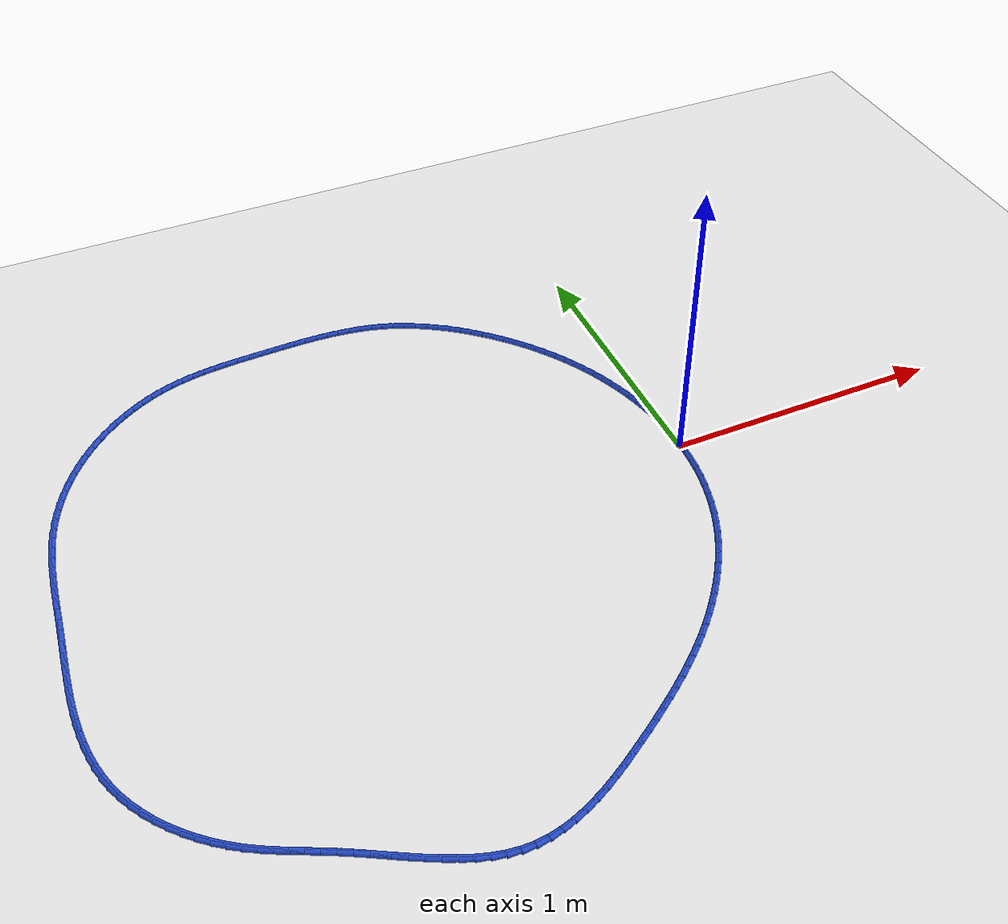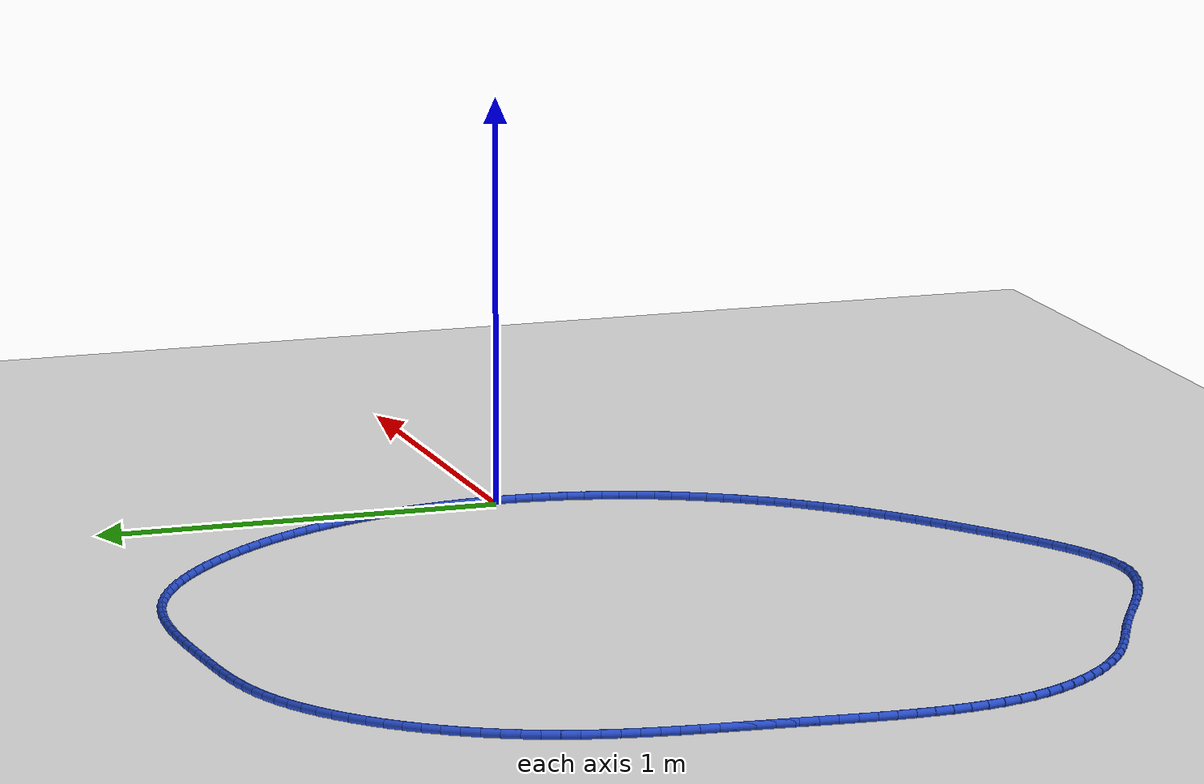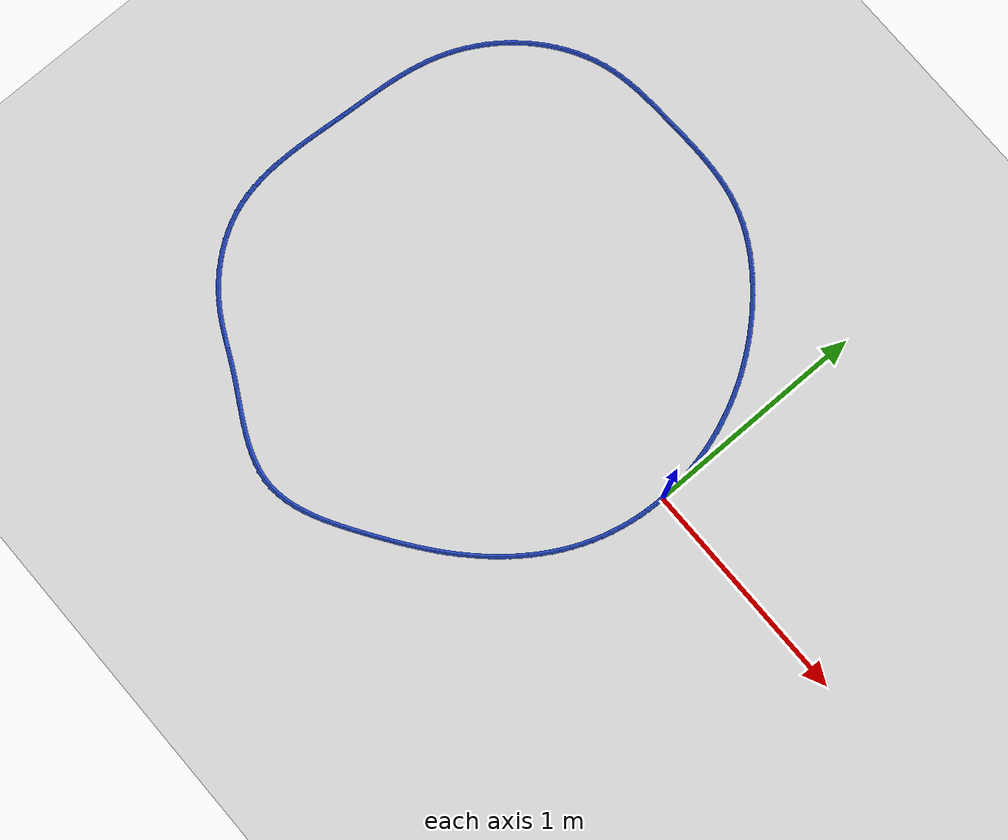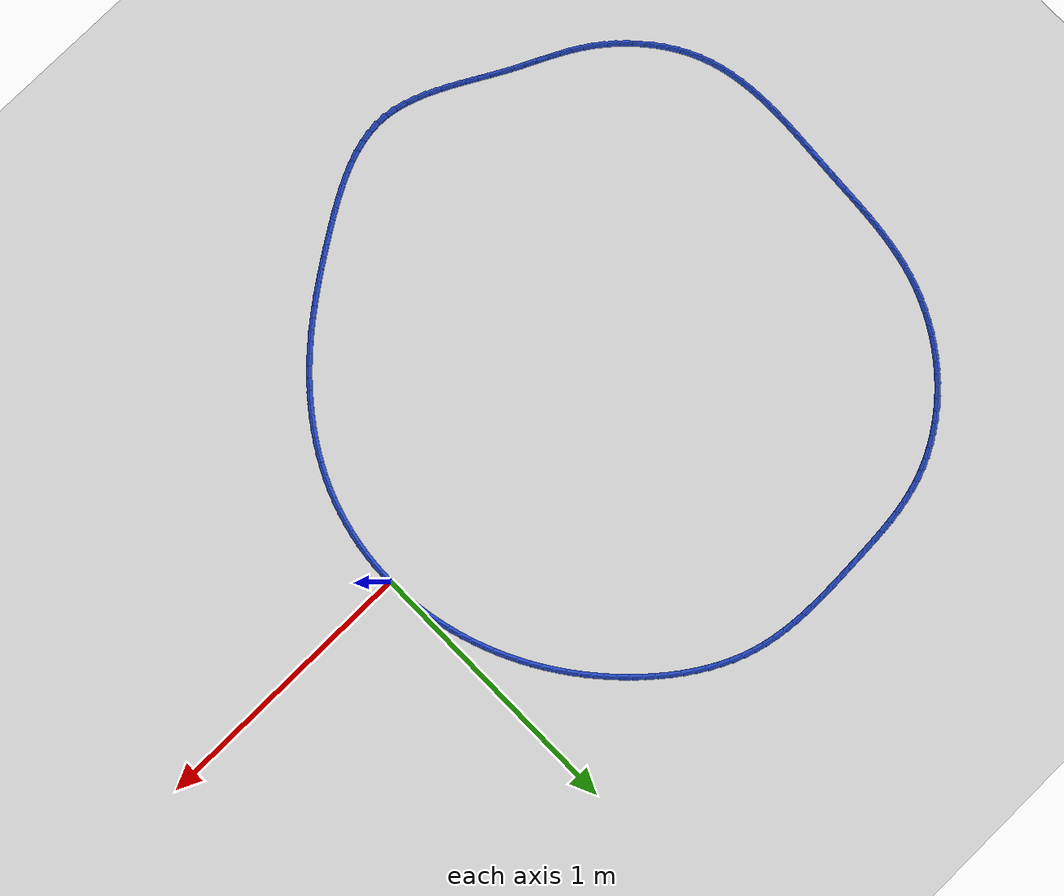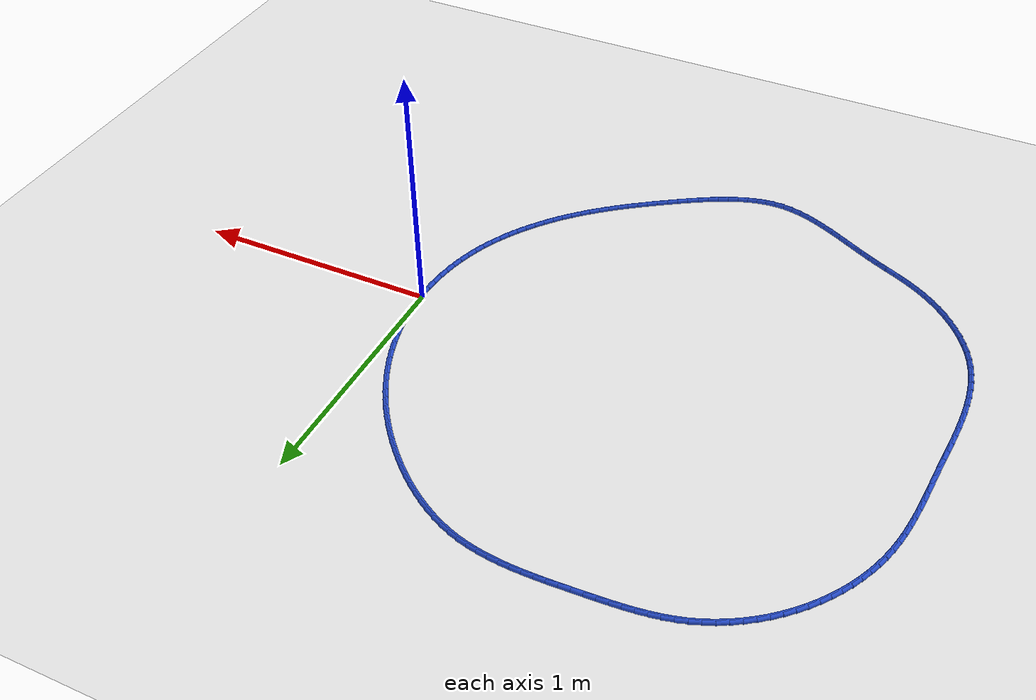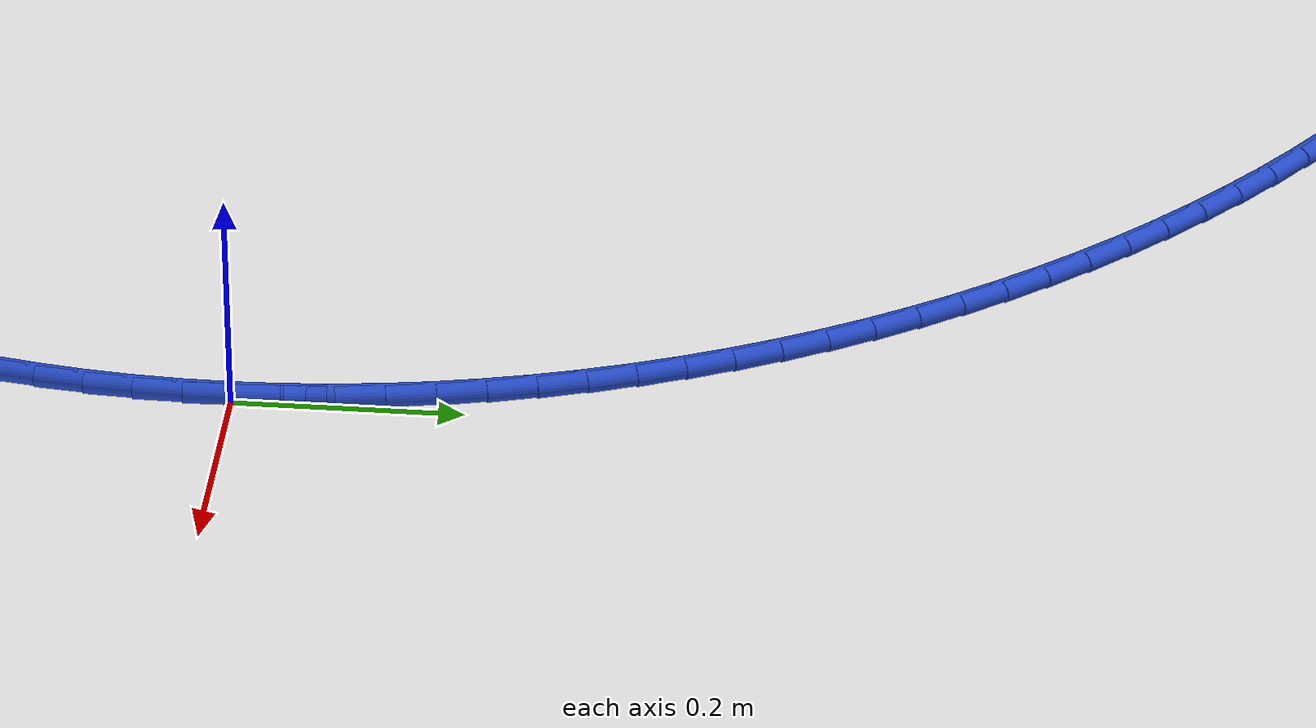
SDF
<sdf version="1.6">
 <world name="default">
  <light name="sun" type="directional">
   <pose>0 0 10 0 -0 0</pose>
   <diffuse>0.8 0.8 0.8 1</diffuse>
   <specular>0.2 0.2 0.2 1</specular>
   <attenuation>
    <range>1000</range>
    <constant>0.9</constant>
    <linear>0.01</linear>
    <quadratic>0.001</quadratic>
   </attenuation>
   <direction>-0.5 0.1 -0.9</direction>
  </light>
  <model name="ground_plane">
   <static>1</static>
   <link name="link">
    <collision name="collision">
     <geometry><plane><normal>0 0 1</normal><size>100 100</size></plane></geometry>
     <surface><friction><ode><mu>100</mu><mu2>50</mu2></ode></friction></surface>
    </collision>
    <visual name="visual">
     <cast_shadows>0</cast_shadows>
     <geometry><plane><normal>0 0 1</normal><size>100 100</size></plane></geometry>
     <material>
      <script><uri>file://media/materials/scripts/gazebo.material</uri><name>Gazebo/WhiteGlow</name></script>
     </material>
    </visual>
   </link>
  </model>
  <gravity>0 0 -9.8</gravity>
  <magnetic_field>6e-06 2.3e-05 -4.2e-05</magnetic_field>
  <atmosphere type="adiabatic"/>
  <physics name="default_physics" default="0" type="ode">
   <max_step_size>0.001</max_step_size>
   <real_time_factor>1</real_time_factor>
   <real_time_update_rate>1000</real_time_update_rate>
  </physics>
  <scene><ambient>0.4 0.4 0.4 1</ambient><background>0.7 0.7 0.7 1</background><shadows>1</shadows></scene>
  <spherical_coordinates>
   <surface_model>EARTH_WGS84</surface_model>
   <latitude_deg>0</latitude_deg>
   <longitude_deg>0</longitude_deg>
   <elevation>0</elevation>
   <heading_deg>0</heading_deg>
  </spherical_coordinates>
  <model name="line">
   <link name="link_0">
    <pose>-1.5612511283791264e-17 -1.3877787807814457e-17 0.01 0 1.57 -1.54260077349949</pose>
    <collision name="collision">
     <geometry><cylinder><radius>0.01</radius><length>0.08</length></cylinder></geometry>
    </collision>
    <visual name="visual">
     <material>
      <script><name>Gazebo/Blue</name><uri>file://media/materials/scripts/gazebo.material</uri></script>
     </material>
     <geometry><cylinder><radius>0.01</radius><length>0.08</length></cylinder></geometry>
    </visual>
   </link>
   <link name="link_1">
    <pose>-0.0012090307983180961 0.04286883040929545 0.01 0 1.57 -1.499397885782941</pose>
    <collision name="collision">
     <geometry><cylinder><radius>0.01</radius><length>0.08</length></cylinder></geometry>
    </collision>
    <visual name="visual">
     <material>
      <script><name>Gazebo/Blue</name><uri>file://media/materials/scripts/gazebo.material</uri></script>
     </material>
     <geometry><cylinder><radius>0.01</radius><length>0.08</length></cylinder></geometry>
    </visual>
   </link>
   <link name="link_2">
    <pose>-0.004267867004953753 0.08563778560639608 0.01 0 1.57 -1.4571062664524819</pose>
    <collision name="collision">
     <geometry><cylinder><radius>0.01</radius><length>0.08</length></cylinder></geometry>
    </collision>
    <visual name="visual">
     <material>
      <script><name>Gazebo/Blue</name><uri>file://media/materials/scripts/gazebo.material</uri></script>
     </material>
     <geometry><cylinder><radius>0.01</radius><length>0.08</length></cylinder></geometry>
    </visual>
   </link>
   <link name="link_3">
    <pose>-0.009132403668698925 0.12824098085870977 0.01 0 1.57 -1.4156710939081507</pose>
    <collision name="collision">
     <geometry><cylinder><radius>0.01</radius><length>0.08</length></cylinder></geometry>
    </collision>
    <visual name="visual">
     <material>
      <script><name>Gazebo/Blue</name><uri>file://media/materials/scripts/gazebo.material</uri></script>
     </material>
     <geometry><cylinder><radius>0.01</radius><length>0.08</length></cylinder></geometry>
    </visual>
   </link>
   <link name="link_4">
    <pose>-0.01575853583834551 0.17061253143364433 0.01 0 1.57 -1.3750280412431315</pose>
    <collision name="collision">
     <geometry><cylinder><radius>0.01</radius><length>0.08</length></cylinder></geometry>
    </collision>
    <visual name="visual">
     <material>
      <script><name>Gazebo/Blue</name><uri>file://media/materials/scripts/gazebo.material</uri></script>
     </material>
     <geometry><cylinder><radius>0.01</radius><length>0.08</length></cylinder></geometry>
    </visual>
   </link>
   <link name="link_5">
    <pose>-0.024102158562685445 0.21268655259860744 0.01 0 1.57 -1.335104849690482</pose>
    <collision name="collision">
     <geometry><cylinder><radius>0.01</radius><length>0.08</length></cylinder></geometry>
    </collision>
    <visual name="visual">
     <material>
      <script><name>Gazebo/Blue</name><uri>file://media/materials/scripts/gazebo.material</uri></script>
     </material>
     <geometry><cylinder><radius>0.01</radius><length>0.08</length></cylinder></geometry>
    </visual>
   </link>
   <link name="link_6">
    <pose>-0.034119166890510665 0.25439715962100706 0.01 0 1.57 -1.2958226904419372</pose>
    <collision name="collision">
     <geometry><cylinder><radius>0.01</radius><length>0.08</length></cylinder></geometry>
    </collision>
    <visual name="visual">
     <material>
      <script><name>Gazebo/Blue</name><uri>file://media/materials/scripts/gazebo.material</uri></script>
     </material>
     <geometry><cylinder><radius>0.01</radius><length>0.08</length></cylinder></geometry>
    </visual>
   </link>
   <link name="link_7">
    <pose>-0.04576545587061305 0.2956784677682508 0.01 0 1.57 -1.25709731164531</pose>
    <collision name="collision">
     <geometry><cylinder><radius>0.01</radius><length>0.08</length></cylinder></geometry>
    </collision>
    <visual name="visual">
     <material>
      <script><name>Gazebo/Blue</name><uri>file://media/materials/scripts/gazebo.material</uri></script>
     </material>
     <geometry><cylinder><radius>0.01</radius><length>0.08</length></cylinder></geometry>
    </visual>
   </link>
   <link name="link_8">
    <pose>-0.05899692055178456 0.3364645923077466 0.01 0 1.57 -1.2188399790968345</pose>
    <collision name="collision">
     <geometry><cylinder><radius>0.01</radius><length>0.08</length></cylinder></geometry>
    </collision>
    <visual name="visual">
     <material>
      <script><name>Gazebo/Blue</name><uri>file://media/materials/scripts/gazebo.material</uri></script>
     </material>
     <geometry><cylinder><radius>0.01</radius><length>0.08</length></cylinder></geometry>
    </visual>
   </link>
   <link name="link_9">
    <pose>-0.07376945598281709 0.3766896485069023 0.01 0 1.57 -1.1809654141339536</pose>
    <collision name="collision">
     <geometry><cylinder><radius>0.01</radius><length>0.08</length></cylinder></geometry>
    </collision>
    <visual name="visual">
     <material>
      <script><name>Gazebo/Blue</name><uri>file://media/materials/scripts/gazebo.material</uri></script>
     </material>
     <geometry><cylinder><radius>0.01</radius><length>0.08</length></cylinder></geometry>
    </visual>
   </link>
   <link name="link_10">
    <pose>-0.09004017008140396 0.4162915132583234 0.01 0 1.57 -1.1434556414480332</pose>
    <collision name="collision">
     <geometry><cylinder><radius>0.01</radius><length>0.08</length></cylinder></geometry>
    </collision>
    <visual name="visual">
     <material>
      <script><name>Gazebo/Blue</name><uri>file://media/materials/scripts/gazebo.material</uri></script>
     </material>
     <geometry><cylinder><radius>0.01</radius><length>0.08</length></cylinder></geometry>
    </visual>
   </link>
   <link name="link_11">
    <pose>-0.10777383144625427 0.45523182250285976 0.01 0 1.57 -1.106322074995886</pose>
    <collision name="collision">
     <geometry><cylinder><radius>0.01</radius><length>0.08</length></cylinder></geometry>
    </collision>
    <visual name="visual">
     <material>
      <script><name>Gazebo/Blue</name><uri>file://media/materials/scripts/gazebo.material</uri></script>
     </material>
     <geometry><cylinder><radius>0.01</radius><length>0.08</length></cylinder></geometry>
    </visual>
   </link>
   <link name="link_12">
    <pose>-0.12693819126342254 0.49348146246034896 0.01 0 1.57 -1.0695628093231606</pose>
    <collision name="collision">
     <geometry><cylinder><radius>0.01</radius><length>0.08</length></cylinder></geometry>
    </collision>
    <visual name="visual">
     <material>
      <script><name>Gazebo/Blue</name><uri>file://media/materials/scripts/gazebo.material</uri></script>
     </material>
     <geometry><cylinder><radius>0.01</radius><length>0.08</length></cylinder></geometry>
    </visual>
   </link>
   <link name="link_13">
    <pose>-0.14750100743375746 0.5310113401760771 0.01 0 1.57 -1.0331719222769677</pose>
    <collision name="collision">
     <geometry><cylinder><radius>0.01</radius><length>0.08</length></cylinder></geometry>
    </collision>
    <visual name="visual">
     <material>
      <script><name>Gazebo/Blue</name><uri>file://media/materials/scripts/gazebo.material</uri></script>
     </material>
     <geometry><cylinder><radius>0.01</radius><length>0.08</length></cylinder></geometry>
    </visual>
   </link>
   <link name="link_14">
    <pose>-0.16943003785810798 0.5677923626953311 0.01 0 1.57 -0.9971398947715384</pose>
    <collision name="collision">
     <geometry><cylinder><radius>0.01</radius><length>0.08</length></cylinder></geometry>
    </collision>
    <visual name="visual">
     <material>
      <script><name>Gazebo/Blue</name><uri>file://media/materials/scripts/gazebo.material</uri></script>
     </material>
     <geometry><cylinder><radius>0.01</radius><length>0.08</length></cylinder></geometry>
    </visual>
   </link>
   <link name="link_15">
    <pose>-0.19269304043732285 0.6037954370633972 0.01 0 1.57 -0.9614539993555775</pose>
    <collision name="collision">
     <geometry><cylinder><radius>0.01</radius><length>0.08</length></cylinder></geometry>
    </collision>
    <visual name="visual">
     <material>
      <script><name>Gazebo/Blue</name><uri>file://media/materials/scripts/gazebo.material</uri></script>
     </material>
     <geometry><cylinder><radius>0.01</radius><length>0.08</length></cylinder></geometry>
    </visual>
   </link>
   <link name="link_16">
    <pose>-0.21725777307225103 0.6389914703255625 0.01 0 1.57 -0.9260986890348469</pose>
    <collision name="collision">
     <geometry><cylinder><radius>0.01</radius><length>0.08</length></cylinder></geometry>
    </collision>
    <visual name="visual">
     <material>
      <script><name>Gazebo/Blue</name><uri>file://media/materials/scripts/gazebo.material</uri></script>
     </material>
     <geometry><cylinder><radius>0.01</radius><length>0.08</length></cylinder></geometry>
    </visual>
   </link>
   <link name="link_17">
    <pose>-0.2430919936637413 0.673351369527113 0.01 0 1.57 -0.891055979728214</pose>
    <collision name="collision">
     <geometry><cylinder><radius>0.01</radius><length>0.08</length></cylinder></geometry>
    </collision>
    <visual name="visual">
     <material>
      <script><name>Gazebo/Blue</name><uri>file://media/materials/scripts/gazebo.material</uri></script>
     </material>
     <geometry><cylinder><radius>0.01</radius><length>0.08</length></cylinder></geometry>
    </visual>
   </link>
   <link name="link_18">
    <pose>-0.27016346011264236 0.7068460417133355 0.01 0 1.57 -0.8563058213647105</pose>
    <collision name="collision">
     <geometry><cylinder><radius>0.01</radius><length>0.08</length></cylinder></geometry>
    </collision>
    <visual name="visual">
     <material>
      <script><name>Gazebo/Blue</name><uri>file://media/materials/scripts/gazebo.material</uri></script>
     </material>
     <geometry><cylinder><radius>0.01</radius><length>0.08</length></cylinder></geometry>
    </visual>
   </link>
   <link name="link_19">
    <pose>-0.2984399303198032 0.7394463939295164 0.01 0 1.57 -0.8218264541184704</pose>
    <collision name="collision">
     <geometry><cylinder><radius>0.01</radius><length>0.08</length></cylinder></geometry>
    </collision>
    <visual name="visual">
     <material>
      <script><name>Gazebo/Blue</name><uri>file://media/materials/scripts/gazebo.material</uri></script>
     </material>
     <geometry><cylinder><radius>0.01</radius><length>0.08</length></cylinder></geometry>
    </visual>
   </link>
   <link name="link_20">
    <pose>-0.32788916218607256 0.7711233332209424 0.01 0 1.57 -0.787594747588751</pose>
    <collision name="collision">
     <geometry><cylinder><radius>0.01</radius><length>0.08</length></cylinder></geometry>
    </collision>
    <visual name="visual">
     <material>
      <script><name>Gazebo/Blue</name><uri>file://media/materials/scripts/gazebo.material</uri></script>
     </material>
     <geometry><cylinder><radius>0.01</radius><length>0.08</length></cylinder></geometry>
    </visual>
   </link>
   <link name="link_21">
    <pose>-0.35847891361229944 0.8018477666329002 0.01 0 1.57 -0.7535687625416</pose>
    <collision name="collision">
     <geometry><cylinder><radius>0.01</radius><length>0.08</length></cylinder></geometry>
    </collision>
    <visual name="visual">
     <material>
      <script><name>Gazebo/Blue</name><uri>file://media/materials/scripts/gazebo.material</uri></script>
     </material>
     <geometry><cylinder><radius>0.01</radius><length>0.08</length></cylinder></geometry>
    </visual>
   </link>
   <link name="link_22">
    <pose>-0.3901768726482254 0.8315894771222807 0.01 0 1.57 -0.7187728610061271</pose>
    <collision name="collision">
     <geometry><cylinder><radius>0.01</radius><length>0.08</length></cylinder></geometry>
    </collision>
    <visual name="visual">
     <material>
      <script><name>Gazebo/Blue</name><uri>file://media/materials/scripts/gazebo.material</uri></script>
     </material>
     <geometry><cylinder><radius>0.01</radius><length>0.08</length></cylinder></geometry>
    </visual>
   </link>
   <link name="link_23">
    <pose>-0.42294711616901254 0.8602601343301706 0.01 0 1.57 -0.6816500478468487</pose>
    <collision name="collision">
     <geometry><cylinder><radius>0.01</radius><length>0.08</length></cylinder></geometry>
    </collision>
    <visual name="visual">
     <material>
      <script><name>Gazebo/Blue</name><uri>file://media/materials/scripts/gazebo.material</uri></script>
     </material>
     <geometry><cylinder><radius>0.01</radius><length>0.08</length></cylinder></geometry>
    </visual>
   </link>
   <link name="link_24">
    <pose>-0.4567484339095905 0.887686323877712 0.01 0 1.57 -0.641815248313914</pose>
    <collision name="collision">
     <geometry><cylinder><radius>0.01</radius><length>0.08</length></cylinder></geometry>
    </collision>
    <visual name="visual">
     <material>
      <script><name>Gazebo/Blue</name><uri>file://media/materials/scripts/gazebo.material</uri></script>
     </material>
     <geometry><cylinder><radius>0.01</radius><length>0.08</length></cylinder></geometry>
    </visual>
   </link>
   <link name="link_25">
    <pose>-0.49153919521280165 0.9136878661694657 0.01 0 1.57 -0.5989822738385835</pose>
    <collision name="collision">
     <geometry><cylinder><radius>0.01</radius><length>0.08</length></cylinder></geometry>
    </collision>
    <visual name="visual">
     <material>
      <script><name>Gazebo/Blue</name><uri>file://media/materials/scripts/gazebo.material</uri></script>
     </material>
     <geometry><cylinder><radius>0.01</radius><length>0.08</length></cylinder></geometry>
    </visual>
   </link>
   <link name="link_26">
    <pose>-0.5272777694214887 0.9380845816099944 0.01 0 1.57 -0.5528632504019215</pose>
    <collision name="collision">
     <geometry><cylinder><radius>0.01</radius><length>0.08</length></cylinder></geometry>
    </collision>
    <visual name="visual">
     <material>
      <script><name>Gazebo/Blue</name><uri>file://media/materials/scripts/gazebo.material</uri></script>
     </material>
     <geometry><cylinder><radius>0.01</radius><length>0.08</length></cylinder></geometry>
    </visual>
   </link>
   <link name="link_27">
    <pose>-0.563922525878494 0.9606962906038589 0.01 0 1.57 -0.5031789023159101</pose>
    <collision name="collision">
     <geometry><cylinder><radius>0.01</radius><length>0.08</length></cylinder></geometry>
    </collision>
    <visual name="visual">
     <material>
      <script><name>Gazebo/Blue</name><uri>file://media/materials/scripts/gazebo.material</uri></script>
     </material>
     <geometry><cylinder><radius>0.01</radius><length>0.08</length></cylinder></geometry>
    </visual>
   </link>
   <link name="link_28">
    <pose>-0.6014318339266597 0.981342813555621 0.01 0 1.57 -0.4496737825767832</pose>
    <collision name="collision">
     <geometry><cylinder><radius>0.01</radius><length>0.08</length></cylinder></geometry>
    </collision>
    <visual name="visual">
     <material>
      <script><name>Gazebo/Blue</name><uri>file://media/materials/scripts/gazebo.material</uri></script>
     </material>
     <geometry><cylinder><radius>0.01</radius><length>0.08</length></cylinder></geometry>
    </visual>
   </link>
   <link name="link_29">
    <pose>-0.6397640629088281 0.9998439708698423 0.01 0 1.57 -0.3921372829768603</pose>
    <collision name="collision">
     <geometry><cylinder><radius>0.01</radius><length>0.08</length></cylinder></geometry>
    </collision>
    <visual name="visual">
     <material>
      <script><name>Gazebo/Blue</name><uri>file://media/materials/scripts/gazebo.material</uri></script>
     </material>
     <geometry><cylinder><radius>0.01</radius><length>0.08</length></cylinder></geometry>
    </visual>
   </link>
   <link name="link_30">
    <pose>-0.678877582167842 1.0160195829510854 0.01 0 1.57 -0.33043101104305267</pose>
    <collision name="collision">
     <geometry><cylinder><radius>0.01</radius><length>0.08</length></cylinder></geometry>
    </collision>
    <visual name="visual">
     <material>
      <script><name>Gazebo/Blue</name><uri>file://media/materials/scripts/gazebo.material</uri></script>
     </material>
     <geometry><cylinder><radius>0.01</radius><length>0.08</length></cylinder></geometry>
    </visual>
   </link>
   <link name="link_31">
    <pose>-0.7187307601438464 1.029689482733615 0.01 0 1.57 -0.26649024651687075</pose>
    <collision name="collision">
     <geometry><cylinder><radius>0.01</radius><length>0.08</length></cylinder></geometry>
    </collision>
    <visual name="visual">
     <material>
      <script><name>Gazebo/Blue</name><uri>file://media/materials/scripts/gazebo.material</uri></script>
     </material>
     <geometry><cylinder><radius>0.01</radius><length>0.08</length></cylinder></geometry>
    </visual>
   </link>
   <link name="link_32">
    <pose>-0.7592759046672358 1.040757626187531 0.01 0 1.57 -0.20721351335880595</pose>
    <collision name="collision">
     <geometry><cylinder><radius>0.01</radius><length>0.08</length></cylinder></geometry>
    </collision>
    <visual name="visual">
     <material>
      <script><name>Gazebo/Blue</name><uri>file://media/materials/scripts/gazebo.material</uri></script>
     </material>
     <geometry><cylinder><radius>0.01</radius><length>0.08</length></cylinder></geometry>
    </visual>
   </link>
   <link name="link_33">
    <pose>-0.8004448166413262 1.0494126114283115 0.01 0 1.57 -0.15433676331437846</pose>
    <collision name="collision">
     <geometry><cylinder><radius>0.01</radius><length>0.08</length></cylinder></geometry>
    </collision>
    <visual name="visual">
     <material>
      <script><name>Gazebo/Blue</name><uri>file://media/materials/scripts/gazebo.material</uri></script>
     </material>
     <geometry><cylinder><radius>0.01</radius><length>0.08</length></cylinder></geometry>
    </visual>
   </link>
   <link name="link_34">
    <pose>-0.84216496390941 1.0559031807118058 0.01 0 1.57 -0.10799103424108641</pose>
    <collision name="collision">
     <geometry><cylinder><radius>0.01</radius><length>0.08</length></cylinder></geometry>
    </collision>
    <visual name="visual">
     <material>
      <script><name>Gazebo/Blue</name><uri>file://media/materials/scripts/gazebo.material</uri></script>
     </material>
     <geometry><cylinder><radius>0.01</radius><length>0.08</length></cylinder></geometry>
    </visual>
   </link>
   <link name="link_35">
    <pose>-0.88436381431478 1.0604780762938633 0.01 0 1.57 -0.06814832924212612</pose>
    <collision name="collision">
     <geometry><cylinder><radius>0.01</radius><length>0.08</length></cylinder></geometry>
    </collision>
    <visual name="visual">
     <material>
      <script><name>Gazebo/Blue</name><uri>file://media/materials/scripts/gazebo.material</uri></script>
     </material>
     <geometry><cylinder><radius>0.01</radius><length>0.08</length></cylinder></geometry>
    </visual>
   </link>
   <link name="link_36">
    <pose>-0.92696883570073 1.063386040430334 0.01 0 1.57 -0.03468151049792702</pose>
    <collision name="collision">
     <geometry><cylinder><radius>0.01</radius><length>0.08</length></cylinder></geometry>
    </collision>
    <visual name="visual">
     <material>
      <script><name>Gazebo/Blue</name><uri>file://media/materials/scripts/gazebo.material</uri></script>
     </material>
     <geometry><cylinder><radius>0.01</radius><length>0.08</length></cylinder></geometry>
    </visual>
   </link>
   <link name="link_37">
    <pose>-0.9699074959105518 1.0648758153770654 0.01 0 1.57 -0.00741490441610716</pose>
    <collision name="collision">
     <geometry><cylinder><radius>0.01</radius><length>0.08</length></cylinder></geometry>
    </collision>
    <visual name="visual">
     <material>
      <script><name>Gazebo/Blue</name><uri>file://media/materials/scripts/gazebo.material</uri></script>
     </material>
     <geometry><cylinder><radius>0.01</radius><length>0.08</length></cylinder></geometry>
    </visual>
   </link>
   <link name="link_38">
    <pose>-1.0131072627875393 1.0651961433899089 0.01 0 1.57 0.013836397803925857</pose>
    <collision name="collision">
     <geometry><cylinder><radius>0.01</radius><length>0.08</length></cylinder></geometry>
    </collision>
    <visual name="visual">
     <material>
      <script><name>Gazebo/Blue</name><uri>file://media/materials/scripts/gazebo.material</uri></script>
     </material>
     <geometry><cylinder><radius>0.01</radius><length>0.08</length></cylinder></geometry>
    </visual>
   </link>
   <link name="link_39">
    <pose>-1.0564956041749847 1.0645957667247128 0.01 0 1.57 0.029237892884742614</pose>
    <collision name="collision">
     <geometry><cylinder><radius>0.01</radius><length>0.08</length></cylinder></geometry>
    </collision>
    <visual name="visual">
     <material>
      <script><name>Gazebo/Blue</name><uri>file://media/materials/scripts/gazebo.material</uri></script>
     </material>
     <geometry><cylinder><radius>0.01</radius><length>0.08</length></cylinder></geometry>
    </visual>
   </link>
   <link name="link_40">
    <pose>-1.0999999879161808 1.0633234276373265 0.01 0 1.57 0.03891584807647052</pose>
    <collision name="collision">
     <geometry><cylinder><radius>0.01</radius><length>0.08</length></cylinder></geometry>
    </collision>
    <visual name="visual">
     <material>
      <script><name>Gazebo/Blue</name><uri>file://media/materials/scripts/gazebo.material</uri></script>
     </material>
     <geometry><cylinder><radius>0.01</radius><length>0.08</length></cylinder></geometry>
    </visual>
   </link>
   <link name="link_41">
    <pose>-1.1435478818544216 1.0616278683835996 0.01 0 1.57 0.04297399263906294</pose>
    <collision name="collision">
     <geometry><cylinder><radius>0.01</radius><length>0.08</length></cylinder></geometry>
    </collision>
    <visual name="visual">
     <material>
      <script><name>Gazebo/Blue</name><uri>file://media/materials/scripts/gazebo.material</uri></script>
     </material>
     <geometry><cylinder><radius>0.01</radius><length>0.08</length></cylinder></geometry>
    </visual>
   </link>
   <link name="link_42">
    <pose>-1.1870667485631647 1.0597565368148603 0.01 0 1.57 0.04549724654629769</pose>
    <collision name="collision">
     <geometry><cylinder><radius>0.01</radius><length>0.08</length></cylinder></geometry>
    </collision>
    <visual name="visual">
     <material>
      <script><name>Gazebo/Blue</name><uri>file://media/materials/scripts/gazebo.material</uri></script>
     </material>
     <geometry><cylinder><radius>0.01</radius><length>0.08</length></cylinder></geometry>
    </visual>
   </link>
   <link name="link_43">
    <pose>-1.2304833298310858 1.0577798378025063 0.01 0 1.57 0.054688654376996035</pose>
    <collision name="collision">
     <geometry><cylinder><radius>0.01</radius><length>0.08</length></cylinder></geometry>
    </collision>
    <visual name="visual">
     <material>
      <script><name>Gazebo/Blue</name><uri>file://media/materials/scripts/gazebo.material</uri></script>
     </material>
     <geometry><cylinder><radius>0.01</radius><length>0.08</length></cylinder></geometry>
    </visual>
   </link>
   <link name="link_44">
    <pose>-1.27372292047146 1.055412762448987 0.01 0 1.57 0.071640880850923</pose>
    <collision name="collision">
     <geometry><cylinder><radius>0.01</radius><length>0.08</length></cylinder></geometry>
    </collision>
    <visual name="visual">
     <material>
      <script><name>Gazebo/Blue</name><uri>file://media/materials/scripts/gazebo.material</uri></script>
     </material>
     <geometry><cylinder><radius>0.01</radius><length>0.08</length></cylinder></geometry>
    </visual>
   </link>
   <link name="link_45">
    <pose>-1.31671064228105 1.052327804623942 0.01 0 1.57 0.09651708608216648</pose>
    <collision name="collision">
     <geometry><cylinder><radius>0.01</radius><length>0.08</length></cylinder></geometry>
    </collision>
    <visual name="visual">
     <material>
      <script><name>Gazebo/Blue</name><uri>file://media/materials/scripts/gazebo.material</uri></script>
     </material>
     <geometry><cylinder><radius>0.01</radius><length>0.08</length></cylinder></geometry>
    </visual>
   </link>
   <link name="link_46">
    <pose>-1.359371617056619 1.048197458197012 0.01 0 1.57 0.12949666245008654</pose>
    <collision name="collision">
     <geometry><cylinder><radius>0.01</radius><length>0.08</length></cylinder></geometry>
    </collision>
    <visual name="visual">
     <material>
      <script><name>Gazebo/Blue</name><uri>file://media/materials/scripts/gazebo.material</uri></script>
     </material>
     <geometry><cylinder><radius>0.01</radius><length>0.08</length></cylinder></geometry>
    </visual>
   </link>
   <link name="link_47">
    <pose>-1.4016309665949298 1.0426942170378364 0.01 0 1.57 0.17072830940406278</pose>
    <collision name="collision">
     <geometry><cylinder><radius>0.01</radius><length>0.08</length></cylinder></geometry>
    </collision>
    <visual name="visual">
     <material>
      <script><name>Gazebo/Blue</name><uri>file://media/materials/scripts/gazebo.material</uri></script>
     </material>
     <geometry><cylinder><radius>0.01</radius><length>0.08</length></cylinder></geometry>
    </visual>
   </link>
   <link name="link_48">
    <pose>-1.443413812692747 1.0354905750160561 0.01 0 1.57 0.22026313822881807</pose>
    <collision name="collision">
     <geometry><cylinder><radius>0.01</radius><length>0.08</length></cylinder></geometry>
    </collision>
    <visual name="visual">
     <material>
      <script><name>Gazebo/Blue</name><uri>file://media/materials/scripts/gazebo.material</uri></script>
     </material>
     <geometry><cylinder><radius>0.01</radius><length>0.08</length></cylinder></geometry>
    </visual>
   </link>
   <link name="link_49">
    <pose>-1.4846452771468315 1.0262590260013114 0.01 0 1.57 0.27796891463724066</pose>
    <collision name="collision">
     <geometry><cylinder><radius>0.01</radius><length>0.08</length></cylinder></geometry>
    </collision>
    <visual name="visual">
     <material>
      <script><name>Gazebo/Blue</name><uri>file://media/materials/scripts/gazebo.material</uri></script>
     </material>
     <geometry><cylinder><radius>0.01</radius><length>0.08</length></cylinder></geometry>
    </visual>
   </link>
   <link name="link_50">
    <pose>-1.5252504817539485 1.0146720638632427 0.01 0 1.57 0.34258813516011516</pose>
    <collision name="collision">
     <geometry><cylinder><radius>0.01</radius><length>0.08</length></cylinder></geometry>
    </collision>
    <visual name="visual">
     <material>
      <script><name>Gazebo/Blue</name><uri>file://media/materials/scripts/gazebo.material</uri></script>
     </material>
     <geometry><cylinder><radius>0.01</radius><length>0.08</length></cylinder></geometry>
    </visual>
   </link>
   <link name="link_51">
    <pose>-1.5651508058358794 1.0004415517963638 0.01 0 1.57 0.40736102534026614</pose>
    <collision name="collision">
     <geometry><cylinder><radius>0.01</radius><length>0.08</length></cylinder></geometry>
    </collision>
    <visual name="visual">
     <material>
      <script><name>Gazebo/Blue</name><uri>file://media/materials/scripts/gazebo.material</uri></script>
     </material>
     <geometry><cylinder><radius>0.01</radius><length>0.08</length></cylinder></geometry>
    </visual>
   </link>
   <link name="link_52">
    <pose>-1.604239536681095 0.9835748698366559 0.01 0 1.57 0.4695504754755869</pose>
    <collision name="collision">
     <geometry><cylinder><radius>0.01</radius><length>0.08</length></cylinder></geometry>
    </collision>
    <visual name="visual">
     <material>
      <script><name>Gazebo/Blue</name><uri>file://media/materials/scripts/gazebo.material</uri></script>
     </material>
     <geometry><cylinder><radius>0.01</radius><length>0.08</length></cylinder></geometry>
    </visual>
   </link>
   <link name="link_53">
    <pose>-1.6423971992710806 0.9642136523337367 0.01 0 1.57 0.5294338836169007</pose>
    <collision name="collision">
     <geometry><cylinder><radius>0.01</radius><length>0.08</length></cylinder></geometry>
    </collision>
    <visual name="visual">
     <material>
      <script><name>Gazebo/Blue</name><uri>file://media/materials/scripts/gazebo.material</uri></script>
     </material>
     <geometry><cylinder><radius>0.01</radius><length>0.08</length></cylinder></geometry>
    </visual>
   </link>
   <link name="link_54">
    <pose>-1.6795042546225791 0.9425002065204494 0.01 0 1.57 0.5873362842401203</pose>
    <collision name="collision">
     <geometry><cylinder><radius>0.01</radius><length>0.08</length></cylinder></geometry>
    </collision>
    <visual name="visual">
     <material>
      <script><name>Gazebo/Blue</name><uri>file://media/materials/scripts/gazebo.material</uri></script>
     </material>
     <geometry><cylinder><radius>0.01</radius><length>0.08</length></cylinder></geometry>
    </visual>
   </link>
   <link name="link_55">
    <pose>-1.715441163752336 0.9185768396296369 0.01 0 1.57 0.6436038562018128</pose>
    <collision name="collision">
     <geometry><cylinder><radius>0.01</radius><length>0.08</length></cylinder></geometry>
    </collision>
    <visual name="visual">
     <material>
      <script><name>Gazebo/Blue</name><uri>file://media/materials/scripts/gazebo.material</uri></script>
     </material>
     <geometry><cylinder><radius>0.01</radius><length>0.08</length></cylinder></geometry>
    </visual>
   </link>
   <link name="link_56">
    <pose>-1.7500883876770943 0.8925858588941408 0.01 0 1.57 0.6985957467551067</pose>
    <collision name="collision">
     <geometry><cylinder><radius>0.01</radius><length>0.08</length></cylinder></geometry>
    </collision>
    <visual name="visual">
     <material>
      <script><name>Gazebo/Blue</name><uri>file://media/materials/scripts/gazebo.material</uri></script>
     </material>
     <geometry><cylinder><radius>0.01</radius><length>0.08</length></cylinder></geometry>
    </visual>
   </link>
   <link name="link_57">
    <pose>-1.7833263874135987 0.8646695715468049 0.01 0 1.57 0.7526790482722773</pose>
    <collision name="collision">
     <geometry><cylinder><radius>0.01</radius><length>0.08</length></cylinder></geometry>
    </collision>
    <visual name="visual">
     <material>
      <script><name>Gazebo/Blue</name><uri>file://media/materials/scripts/gazebo.material</uri></script>
     </material>
     <geometry><cylinder><radius>0.01</radius><length>0.08</length></cylinder></geometry>
    </visual>
   </link>
   <link name="link_58">
    <pose>-1.8150356239785936 0.8349702848204716 0.01 0 1.57 0.8062163610661034</pose>
    <collision name="collision">
     <geometry><cylinder><radius>0.01</radius><length>0.08</length></cylinder></geometry>
    </collision>
    <visual name="visual">
     <material>
      <script><name>Gazebo/Blue</name><uri>file://media/materials/scripts/gazebo.material</uri></script>
     </material>
     <geometry><cylinder><radius>0.01</radius><length>0.08</length></cylinder></geometry>
    </visual>
   </link>
   <link name="link_59">
    <pose>-1.8450973321621358 0.8036301155149089 0.01 0 1.57 0.8592060650942486</pose>
    <collision name="collision">
     <geometry><cylinder><radius>0.01</radius><length>0.08</length></cylinder></geometry>
    </collision>
    <visual name="visual">
     <material>
      <script><name>Gazebo/Blue</name><uri>file://media/materials/scripts/gazebo.material</uri></script>
     </material>
     <geometry><cylinder><radius>0.01</radius><length>0.08</length></cylinder></geometry>
    </visual>
   </link>
   <link name="link_60">
    <pose>-1.8734200637000045 0.770784457466101 0.01 0 1.57 0.9114390767024368</pose>
    <collision name="collision">
     <geometry><cylinder><radius>0.01</radius><length>0.08</length></cylinder></geometry>
    </collision>
    <visual name="visual">
     <material>
      <script><name>Gazebo/Blue</name><uri>file://media/materials/scripts/gazebo.material</uri></script>
     </material>
     <geometry><cylinder><radius>0.01</radius><length>0.08</length></cylinder></geometry>
    </visual>
   </link>
   <link name="link_61">
    <pose>-1.8999463352491806 0.7365603454153693 0.01 0 1.57 0.9630806245628225</pose>
    <collision name="collision">
     <geometry><cylinder><radius>0.01</radius><length>0.08</length></cylinder></geometry>
    </collision>
    <visual name="visual">
     <material>
      <script><name>Gazebo/Blue</name><uri>file://media/materials/scripts/gazebo.material</uri></script>
     </material>
     <geometry><cylinder><radius>0.01</radius><length>0.08</length></cylinder></geometry>
    </visual>
   </link>
   <link name="link_62">
    <pose>-1.9246207866417273 0.7010842915701726 0.01 0 1.57 1.014334601743101</pose>
    <collision name="collision">
     <geometry><cylinder><radius>0.01</radius><length>0.08</length></cylinder></geometry>
    </collision>
    <visual name="visual">
     <material>
      <script><name>Gazebo/Blue</name><uri>file://media/materials/scripts/gazebo.material</uri></script>
     </material>
     <geometry><cylinder><radius>0.01</radius><length>0.08</length></cylinder></geometry>
    </visual>
   </link>
   <link name="link_63">
    <pose>-1.9473880577097087 0.664482808137969 0.01 0 1.57 1.0654143263387625</pose>
    <collision name="collision">
     <geometry><cylinder><radius>0.01</radius><length>0.08</length></cylinder></geometry>
    </collision>
    <visual name="visual">
     <material>
      <script><name>Gazebo/Blue</name><uri>file://media/materials/scripts/gazebo.material</uri></script>
     </material>
     <geometry><cylinder><radius>0.01</radius><length>0.08</length></cylinder></geometry>
    </visual>
   </link>
   <link name="link_64">
    <pose>-1.968192788285188 0.6268824073262174 0.01 0 1.57 1.116540724287314</pose>
    <collision name="collision">
     <geometry><cylinder><radius>0.01</radius><length>0.08</length></cylinder></geometry>
    </collision>
    <visual name="visual">
     <material>
      <script><name>Gazebo/Blue</name><uri>file://media/materials/scripts/gazebo.material</uri></script>
     </material>
     <geometry><cylinder><radius>0.01</radius><length>0.08</length></cylinder></geometry>
    </visual>
   </link>
   <link name="link_65">
    <pose>-1.9869796182002288 0.5884096013423755 0.01 0 1.57 1.1679407898314</pose>
    <collision name="collision">
     <geometry><cylinder><radius>0.01</radius><length>0.08</length></cylinder></geometry>
    </collision>
    <visual name="visual">
     <material>
      <script><name>Gazebo/Blue</name><uri>file://media/materials/scripts/gazebo.material</uri></script>
     </material>
     <geometry><cylinder><radius>0.01</radius><length>0.08</length></cylinder></geometry>
    </visual>
   </link>
   <link name="link_66">
    <pose>-2.0036931872868946 0.5491909023939018 0.01 0 1.57 1.21984610748962</pose>
    <collision name="collision">
     <geometry><cylinder><radius>0.01</radius><length>0.08</length></cylinder></geometry>
    </collision>
    <visual name="visual">
     <material>
      <script><name>Gazebo/Blue</name><uri>file://media/materials/scripts/gazebo.material</uri></script>
     </material>
     <geometry><cylinder><radius>0.01</radius><length>0.08</length></cylinder></geometry>
    </visual>
   </link>
   <link name="link_67">
    <pose>-2.018278135377249 0.5093528226882549 0.01 0 1.57 1.2719468618733722</pose>
    <collision name="collision">
     <geometry><cylinder><radius>0.01</radius><length>0.08</length></cylinder></geometry>
    </collision>
    <visual name="visual">
     <material>
      <script><name>Gazebo/Blue</name><uri>file://media/materials/scripts/gazebo.material</uri></script>
     </material>
     <geometry><cylinder><radius>0.01</radius><length>0.08</length></cylinder></geometry>
    </visual>
   </link>
   <link name="link_68">
    <pose>-2.0307059994684904 0.46901257772643123 0.01 0 1.57 1.3205071918890698</pose>
    <collision name="collision">
     <geometry><cylinder><radius>0.01</radius><length>0.08</length></cylinder></geometry>
    </collision>
    <visual name="visual">
     <material>
      <script><name>Gazebo/Blue</name><uri>file://media/materials/scripts/gazebo.material</uri></script>
     </material>
     <geometry><cylinder><radius>0.01</radius><length>0.08</length></cylinder></geometry>
    </visual>
   </link>
   <link name="link_69">
    <pose>-2.0411337807512457 0.42822327937037247 0.01 0 1.57 1.3636110490072781</pose>
    <collision name="collision">
     <geometry><cylinder><radius>0.01</radius><length>0.08</length></cylinder></geometry>
    </collision>
    <visual name="visual">
     <material>
      <script><name>Gazebo/Blue</name><uri>file://media/materials/scripts/gazebo.material</uri></script>
     </material>
     <geometry><cylinder><radius>0.01</radius><length>0.08</length></cylinder></geometry>
    </visual>
   </link>
   <link name="link_70">
    <pose>-2.0497966647417125 0.3870110159380493 0.01 0 1.57 1.4010078977996137</pose>
    <collision name="collision">
     <geometry><cylinder><radius>0.01</radius><length>0.08</length></cylinder></geometry>
    </collision>
    <visual name="visual">
     <material>
      <script><name>Gazebo/Blue</name><uri>file://media/materials/scripts/gazebo.material</uri></script>
     </material>
     <geometry><cylinder><radius>0.01</radius><length>0.08</length></cylinder></geometry>
    </visual>
   </link>
   <link name="link_71">
    <pose>-2.056930111427281 0.345401780879511 0.01 0 1.57 1.432582686012051</pose>
    <collision name="collision">
     <geometry><cylinder><radius>0.01</radius><length>0.08</length></cylinder></geometry>
    </collision>
    <visual name="visual">
     <material>
      <script><name>Gazebo/Blue</name><uri>file://media/materials/scripts/gazebo.material</uri></script>
     </material>
     <geometry><cylinder><radius>0.01</radius><length>0.08</length></cylinder></geometry>
    </visual>
   </link>
   <link name="link_72">
    <pose>-2.0627695807953437 0.3034215676448083 0.01 0 1.57 1.4583155238267624</pose>
    <collision name="collision">
     <geometry><cylinder><radius>0.01</radius><length>0.08</length></cylinder></geometry>
    </collision>
    <visual name="visual">
     <material>
      <script><name>Gazebo/Blue</name><uri>file://media/materials/scripts/gazebo.material</uri></script>
     </material>
     <geometry><cylinder><radius>0.01</radius><length>0.08</length></cylinder></geometry>
    </visual>
   </link>
   <link name="link_73">
    <pose>-2.0675505328332924 0.26109636968399014 0.01 0 1.57 1.4782494028792281</pose>
    <collision name="collision">
     <geometry><cylinder><radius>0.01</radius><length>0.08</length></cylinder></geometry>
    </collision>
    <visual name="visual">
     <material>
      <script><name>Gazebo/Blue</name><uri>file://media/materials/scripts/gazebo.material</uri></script>
     </material>
     <geometry><cylinder><radius>0.01</radius><length>0.08</length></cylinder></geometry>
    </visual>
   </link>
   <link name="link_74">
    <pose>-2.0715084275285185 0.21845218044710726 0.01 0 1.57 1.4924632712090597</pose>
    <collision name="collision">
     <geometry><cylinder><radius>0.01</radius><length>0.08</length></cylinder></geometry>
    </collision>
    <visual name="visual">
     <material>
      <script><name>Gazebo/Blue</name><uri>file://media/materials/scripts/gazebo.material</uri></script>
     </material>
     <geometry><cylinder><radius>0.01</radius><length>0.08</length></cylinder></geometry>
    </visual>
   </link>
   <link name="link_75">
    <pose>-2.0748787248684133 0.175514993384209 0.01 0 1.57 1.501051598069755</pose>
    <collision name="collision">
     <geometry><cylinder><radius>0.01</radius><length>0.08</length></cylinder></geometry>
    </collision>
    <visual name="visual">
     <material>
      <script><name>Gazebo/Blue</name><uri>file://media/materials/scripts/gazebo.material</uri></script>
     </material>
     <geometry><cylinder><radius>0.01</radius><length>0.08</length></cylinder></geometry>
    </visual>
   </link>
   <link name="link_76">
    <pose>-2.077896884840369 0.1323108019453449 0.01 0 1.57 1.5041104744818328</pose>
    <collision name="collision">
     <geometry><cylinder><radius>0.01</radius><length>0.08</length></cylinder></geometry>
    </collision>
    <visual name="visual">
     <material>
      <script><name>Gazebo/Blue</name><uri>file://media/materials/scripts/gazebo.material</uri></script>
     </material>
     <geometry><cylinder><radius>0.01</radius><length>0.08</length></cylinder></geometry>
    </visual>
   </link>
   <link name="link_77">
    <pose>-2.080798367431777 0.08886559958056553 0.01 0 1.57 1.501729765323738</pose>
    <collision name="collision">
     <geometry><cylinder><radius>0.01</radius><length>0.08</length></cylinder></geometry>
    </collision>
    <visual name="visual">
     <material>
      <script><name>Gazebo/Blue</name><uri>file://media/materials/scripts/gazebo.material</uri></script>
     </material>
     <geometry><cylinder><radius>0.01</radius><length>0.08</length></cylinder></geometry>
    </visual>
   </link>
   <link name="link_78">
    <pose>-2.083818632630029 0.04520537973991995 0.01 0 1.57 1.4953007910001141</pose>
    <collision name="collision">
     <geometry><cylinder><radius>0.01</radius><length>0.08</length></cylinder></geometry>
    </collision>
    <visual name="visual">
     <material>
      <script><name>Gazebo/Blue</name><uri>file://media/materials/scripts/gazebo.material</uri></script>
     </material>
     <geometry><cylinder><radius>0.01</radius><length>0.08</length></cylinder></geometry>
    </visual>
   </link>
   <link name="link_79">
    <pose>-2.0871349137902775 0.0013620151663336316 0.01 0 1.57 1.4919558046745152</pose>
    <collision name="collision">
     <geometry><cylinder><radius>0.01</radius><length>0.08</length></cylinder></geometry>
    </collision>
    <visual name="visual">
     <material>
      <script><name>Gazebo/Blue</name><uri>file://media/materials/scripts/gazebo.material</uri></script>
     </material>
     <geometry><cylinder><radius>0.01</radius><length>0.08</length></cylinder></geometry>
    </visual>
   </link>
   <link name="link_80">
    <pose>-2.0906081553578835 -0.042600684892233606 0.01 0 1.57 1.494045332599061</pose>
    <collision name="collision">
     <geometry><cylinder><radius>0.01</radius><length>0.08</length></cylinder></geometry>
    </collision>
    <visual name="visual">
     <material>
      <script><name>Gazebo/Blue</name><uri>file://media/materials/scripts/gazebo.material</uri></script>
     </material>
     <geometry><cylinder><radius>0.01</radius><length>0.08</length></cylinder></geometry>
    </visual>
   </link>
   <link name="link_81">
    <pose>-2.093992417515544 -0.08660811880880613 0.01 0 1.57 1.5015704093083702</pose>
    <collision name="collision">
     <geometry><cylinder><radius>0.01</radius><length>0.08</length></cylinder></geometry>
    </collision>
    <visual name="visual">
     <material>
      <script><name>Gazebo/Blue</name><uri>file://media/materials/scripts/gazebo.material</uri></script>
     </material>
     <geometry><cylinder><radius>0.01</radius><length>0.08</length></cylinder></geometry>
    </visual>
   </link>
   <link name="link_82">
    <pose>-2.097041676767747 -0.13058567650720515 0.01 0 1.57 1.5145970750496531</pose>
    <collision name="collision">
     <geometry><cylinder><radius>0.01</radius><length>0.08</length></cylinder></geometry>
    </collision>
    <visual name="visual">
     <material>
      <script><name>Gazebo/Blue</name><uri>file://media/materials/scripts/gazebo.material</uri></script>
     </material>
     <geometry><cylinder><radius>0.01</radius><length>0.08</length></cylinder></geometry>
    </visual>
   </link>
   <link name="link_83">
    <pose>-2.0995099096189813 -0.17445874791124963 0.01 0 1.57 1.5332531231181326</pose>
    <collision name="collision">
     <geometry><cylinder><radius>0.01</radius><length>0.08</length></cylinder></geometry>
    </collision>
    <visual name="visual">
     <material>
      <script><name>Gazebo/Blue</name><uri>file://media/materials/scripts/gazebo.material</uri></script>
     </material>
     <geometry><cylinder><radius>0.01</radius><length>0.08</length></cylinder></geometry>
    </visual>
   </link>
   <link name="link_84">
    <pose>-2.1011510925737364 -0.21815272294476074 0.01 0 1.57 1.5577191245554123</pose>
    <collision name="collision">
     <geometry><cylinder><radius>0.01</radius><length>0.08</length></cylinder></geometry>
    </collision>
    <visual name="visual">
     <material>
      <script><name>Gazebo/Blue</name><uri>file://media/materials/scripts/gazebo.material</uri></script>
     </material>
     <geometry><cylinder><radius>0.01</radius><length>0.08</length></cylinder></geometry>
    </visual>
   </link>
   <link name="link_85">
    <pose>-2.101719202136501 -0.26159299153155885 0.01 0 1.57 -1.5533786190996064</pose>
    <collision name="collision">
     <geometry><cylinder><radius>0.01</radius><length>0.08</length></cylinder></geometry>
    </collision>
    <visual name="visual">
     <material>
      <script><name>Gazebo/Blue</name><uri>file://media/materials/scripts/gazebo.material</uri></script>
     </material>
     <geometry><cylinder><radius>0.01</radius><length>0.08</length></cylinder></geometry>
    </visual>
   </link>
   <link name="link_86">
    <pose>-2.1009682148117634 -0.3047049435954646 0.01 0 1.57 -1.516619458768519</pose>
    <collision name="collision">
     <geometry><cylinder><radius>0.01</radius><length>0.08</length></cylinder></geometry>
    </collision>
    <visual name="visual">
     <material>
      <script><name>Gazebo/Blue</name><uri>file://media/materials/scripts/gazebo.material</uri></script>
     </material>
     <geometry><cylinder><radius>0.01</radius><length>0.08</length></cylinder></geometry>
    </visual>
   </link>
   <link name="link_87">
    <pose>-2.0986521071040123 -0.3474139690602991 0.01 0 1.57 -1.4733764466963872</pose>
    <collision name="collision">
     <geometry><cylinder><radius>0.01</radius><length>0.08</length></cylinder></geometry>
    </collision>
    <visual name="visual">
     <material>
      <script><name>Gazebo/Blue</name><uri>file://media/materials/scripts/gazebo.material</uri></script>
     </material>
     <geometry><cylinder><radius>0.01</radius><length>0.08</length></cylinder></geometry>
    </visual>
   </link>
   <link name="link_88">
    <pose>-2.0945248555177374 -0.38964545784988125 0.01 0 1.57 -1.423490210040717</pose>
    <collision name="collision">
     <geometry><cylinder><radius>0.01</radius><length>0.08</length></cylinder></geometry>
    </collision>
    <visual name="visual">
     <material>
      <script><name>Gazebo/Blue</name><uri>file://media/materials/scripts/gazebo.material</uri></script>
     </material>
     <geometry><cylinder><radius>0.01</radius><length>0.08</length></cylinder></geometry>
    </visual>
   </link>
   <link name="link_89">
    <pose>-2.0883404365574267 -0.4313247998880324 0.01 0 1.57 -1.3669191713253421</pose>
    <collision name="collision">
     <geometry><cylinder><radius>0.01</radius><length>0.08</length></cylinder></geometry>
    </collision>
    <visual name="visual">
     <material>
      <script><name>Gazebo/Blue</name><uri>file://media/materials/scripts/gazebo.material</uri></script>
     </material>
     <geometry><cylinder><radius>0.01</radius><length>0.08</length></cylinder></geometry>
    </visual>
   </link>
   <link name="link_90">
    <pose>-2.0798528267275693 -0.47237738509857286 0.01 0 1.57 -1.3038075262631823</pose>
    <collision name="collision">
     <geometry><cylinder><radius>0.01</radius><length>0.08</length></cylinder></geometry>
    </collision>
    <visual name="visual">
     <material>
      <script><name>Gazebo/Blue</name><uri>file://media/materials/scripts/gazebo.material</uri></script>
     </material>
     <geometry><cylinder><radius>0.01</radius><length>0.08</length></cylinder></geometry>
    </visual>
   </link>
   <link name="link_91">
    <pose>-2.0688160025326536 -0.5127286034053231 0.01 0 1.57 -1.2345554097578193</pose>
    <collision name="collision">
     <geometry><cylinder><radius>0.01</radius><length>0.08</length></cylinder></geometry>
    </collision>
    <visual name="visual">
     <material>
      <script><name>Gazebo/Blue</name><uri>file://media/materials/scripts/gazebo.material</uri></script>
     </material>
     <geometry><cylinder><radius>0.01</radius><length>0.08</length></cylinder></geometry>
    </visual>
   </link>
   <link name="link_92">
    <pose>-2.0549839404771686 -0.5523038447321043 0.01 0 1.57 -1.1602242989047704</pose>
    <collision name="collision">
     <geometry><cylinder><radius>0.01</radius><length>0.08</length></cylinder></geometry>
    </collision>
    <visual name="visual">
     <material>
      <script><name>Gazebo/Blue</name><uri>file://media/materials/scripts/gazebo.material</uri></script>
     </material>
     <geometry><cylinder><radius>0.01</radius><length>0.08</length></cylinder></geometry>
    </visual>
   </link>
   <link name="link_93">
    <pose>-2.038128051842379 -0.5910252894344553 0.01 0 1.57 -1.0866201047593649</pose>
    <collision name="collision">
     <geometry><cylinder><radius>0.01</radius><length>0.08</length></cylinder></geometry>
    </collision>
    <visual name="visual">
     <material>
      <script><name>Gazebo/Blue</name><uri>file://media/materials/scripts/gazebo.material</uri></script>
     </material>
     <geometry><cylinder><radius>0.01</radius><length>0.08</length></cylinder></geometry>
    </visual>
   </link>
   <link name="link_94">
    <pose>-2.018278254097147 -0.6287675294605217 0.01 0 1.57 -1.0173168560609367</pose>
    <collision name="collision">
     <geometry><cylinder><radius>0.01</radius><length>0.08</length></cylinder></geometry>
    </collision>
    <visual name="visual">
     <material>
      <script><name>Gazebo/Blue</name><uri>file://media/materials/scripts/gazebo.material</uri></script>
     </material>
     <geometry><cylinder><radius>0.01</radius><length>0.08</length></cylinder></geometry>
    </visual>
   </link>
   <link name="link_95">
    <pose>-1.9956622582120465 -0.66536874495018 0.01 0 1.57 -0.9517296497552693</pose>
    <collision name="collision">
     <geometry><cylinder><radius>0.01</radius><length>0.08</length></cylinder></geometry>
    </collision>
    <visual name="visual">
     <material>
      <script><name>Gazebo/Blue</name><uri>file://media/materials/scripts/gazebo.material</uri></script>
     </material>
     <geometry><cylinder><radius>0.01</radius><length>0.08</length></cylinder></geometry>
    </visual>
   </link>
   <link name="link_96">
    <pose>-1.97051279397164 -0.7006661921297738 0.01 0 1.57 -0.889146601270404</pose>
    <collision name="collision">
     <geometry><cylinder><radius>0.01</radius><length>0.08</length></cylinder></geometry>
    </collision>
    <visual name="visual">
     <material>
      <script><name>Gazebo/Blue</name><uri>file://media/materials/scripts/gazebo.material</uri></script>
     </material>
     <geometry><cylinder><radius>0.01</radius><length>0.08</length></cylinder></geometry>
    </visual>
   </link>
   <link name="link_97">
    <pose>-1.9430625911604957 -0.7344971272256461 0.01 0 1.57 -0.8288489638059063</pose>
    <collision name="collision">
     <geometry><cylinder><radius>0.01</radius><length>0.08</length></cylinder></geometry>
    </collision>
    <visual name="visual">
     <material>
      <script><name>Gazebo/Blue</name><uri>file://media/materials/scripts/gazebo.material</uri></script>
     </material>
     <geometry><cylinder><radius>0.01</radius><length>0.08</length></cylinder></geometry>
    </visual>
   </link>
   <link name="link_98">
    <pose>-1.9135443795631748 -0.7666988064641409 0.01 0 1.57 -0.7701182233524391</pose>
    <collision name="collision">
     <geometry><cylinder><radius>0.01</radius><length>0.08</length></cylinder></geometry>
    </collision>
    <visual name="visual">
     <material>
      <script><name>Gazebo/Blue</name><uri>file://media/materials/scripts/gazebo.material</uri></script>
     </material>
     <geometry><cylinder><radius>0.01</radius><length>0.08</length></cylinder></geometry>
    </visual>
   </link>
   <link name="link_99">
    <pose>-1.8821908889642434 -0.797108486071602 0.01 0 1.57 -0.7122342174187738</pose>
    <collision name="collision">
     <geometry><cylinder><radius>0.01</radius><length>0.08</length></cylinder></geometry>
    </collision>
    <visual name="visual">
     <material>
      <script><name>Gazebo/Blue</name><uri>file://media/materials/scripts/gazebo.material</uri></script>
     </material>
     <geometry><cylinder><radius>0.01</radius><length>0.08</length></cylinder></geometry>
    </visual>
   </link>
   <link name="link_100">
    <pose>-1.849234849148266 -0.8255634222743731 0.01 0 1.57 -0.6544671290147033</pose>
    <collision name="collision">
     <geometry><cylinder><radius>0.01</radius><length>0.08</length></cylinder></geometry>
    </collision>
    <visual name="visual">
     <material>
      <script><name>Gazebo/Blue</name><uri>file://media/materials/scripts/gazebo.material</uri></script>
     </material>
     <geometry><cylinder><radius>0.01</radius><length>0.08</length></cylinder></geometry>
    </visual>
   </link>
   <link name="link_101">
    <pose>-1.814908989899806 -0.8519008712987979 0.01 0 1.57 -0.5960750755200789</pose>
    <collision name="collision">
     <geometry><cylinder><radius>0.01</radius><length>0.08</length></cylinder></geometry>
    </collision>
    <visual name="visual">
     <material>
      <script><name>Gazebo/Blue</name><uri>file://media/materials/scripts/gazebo.material</uri></script>
     </material>
     <geometry><cylinder><radius>0.01</radius><length>0.08</length></cylinder></geometry>
    </visual>
   </link>
   <link name="link_102">
    <pose>-1.7794459726980365 -0.8759586364331196 0.01 0 1.57 -0.5399700237985333</pose>
    <collision name="collision">
     <geometry><cylinder><radius>0.01</radius><length>0.08</length></cylinder></geometry>
    </collision>
    <visual name="visual">
     <material>
      <script><name>Gazebo/Blue</name><uri>file://media/materials/scripts/gazebo.material</uri></script>
     </material>
     <geometry><cylinder><radius>0.01</radius><length>0.08</length></cylinder></geometry>
    </visual>
   </link>
   <link name="link_103">
    <pose>-1.7430538427240991 -0.8977716743413989 0.01 0 1.57 -0.4955046062098071</pose>
    <collision name="collision">
     <geometry><cylinder><radius>0.01</radius><length>0.08</length></cylinder></geometry>
    </collision>
    <visual name="visual">
     <material>
      <script><name>Gazebo/Blue</name><uri>file://media/materials/scripts/gazebo.material</uri></script>
     </material>
     <geometry><cylinder><radius>0.01</radius><length>0.08</length></cylinder></geometry>
    </visual>
   </link>
   <link name="link_104">
    <pose>-1.7058796344399103 -0.917863580119115 0.01 0 1.57 -0.46490541975444255</pose>
    <collision name="collision">
     <geometry><cylinder><radius>0.01</radius><length>0.08</length></cylinder></geometry>
    </collision>
    <visual name="visual">
     <material>
      <script><name>Gazebo/Blue</name><uri>file://media/materials/scripts/gazebo.material</uri></script>
     </material>
     <geometry><cylinder><radius>0.01</radius><length>0.08</length></cylinder></geometry>
    </visual>
   </link>
   <link name="link_105">
    <pose>-1.668061092796275 -0.9368323491014806 0.01 0 1.57 -0.4485281783276075</pose>
    <collision name="collision">
     <geometry><cylinder><radius>0.01</radius><length>0.08</length></cylinder></geometry>
    </collision>
    <visual name="visual">
     <material>
      <script><name>Gazebo/Blue</name><uri>file://media/materials/scripts/gazebo.material</uri></script>
     </material>
     <geometry><cylinder><radius>0.01</radius><length>0.08</length></cylinder></geometry>
    </visual>
   </link>
   <link name="link_106">
    <pose>-1.6297359627440002 -0.9552759766237111 0.01 0 1.57 -0.4463299033197552</pose>
    <collision name="collision">
     <geometry><cylinder><radius>0.01</radius><length>0.08</length></cylinder></geometry>
    </collision>
    <visual name="visual">
     <material>
      <script><name>Gazebo/Blue</name><uri>file://media/materials/scripts/gazebo.material</uri></script>
     </material>
     <geometry><cylinder><radius>0.01</radius><length>0.08</length></cylinder></geometry>
    </visual>
   </link>
   <link name="link_107">
    <pose>-1.591041989233893 -0.9737924580210193 0.01 0 1.57 -0.457975523023273</pose>
    <collision name="collision">
     <geometry><cylinder><radius>0.01</radius><length>0.08</length></cylinder></geometry>
    </collision>
    <visual name="visual">
     <material>
      <script><name>Gazebo/Blue</name><uri>file://media/materials/scripts/gazebo.material</uri></script>
     </material>
     <geometry><cylinder><radius>0.01</radius><length>0.08</length></cylinder></geometry>
    </visual>
   </link>
   <link name="link_108">
    <pose>-1.5521169172167602 -0.9929797886286197 0.01 0 1.57 -0.48061842126913606</pose>
    <collision name="collision">
     <geometry><cylinder><radius>0.01</radius><length>0.08</length></cylinder></geometry>
    </collision>
    <visual name="visual">
     <material>
      <script><name>Gazebo/Blue</name><uri>file://media/materials/scripts/gazebo.material</uri></script>
     </material>
     <geometry><cylinder><radius>0.01</radius><length>0.08</length></cylinder></geometry>
    </visual>
   </link>
   <link name="link_109">
    <pose>-1.5130852212822274 -1.0133308029820065 0.01 0 1.57 -0.49851467447994907</pose>
    <collision name="collision">
     <geometry><cylinder><radius>0.01</radius><length>0.08</length></cylinder></geometry>
    </collision>
    <visual name="visual">
     <material>
      <script><name>Gazebo/Blue</name><uri>file://media/materials/scripts/gazebo.material</uri></script>
     </material>
     <geometry><cylinder><radius>0.01</radius><length>0.08</length></cylinder></geometry>
    </visual>
   </link>
   <link name="link_110">
    <pose>-1.4739805310417118 -1.034618435801638 0.01 0 1.57 -0.5056897653478503</pose>
    <collision name="collision">
     <geometry><cylinder><radius>0.01</radius><length>0.08</length></cylinder></geometry>
    </collision>
    <visual name="visual">
     <material>
      <script><name>Gazebo/Blue</name><uri>file://media/materials/scripts/gazebo.material</uri></script>
     </material>
     <geometry><cylinder><radius>0.01</radius><length>0.08</length></cylinder></geometry>
    </visual>
   </link>
   <link name="link_111">
    <pose>-1.4347984260643727 -1.0563140947569165 0.01 0 1.57 -0.5024291813071842</pose>
    <collision name="collision">
     <geometry><cylinder><radius>0.01</radius><length>0.08</length></cylinder></geometry>
    </collision>
    <visual name="visual">
     <material>
      <script><name>Gazebo/Blue</name><uri>file://media/materials/scripts/gazebo.material</uri></script>
     </material>
     <geometry><cylinder><radius>0.01</radius><length>0.08</length></cylinder></geometry>
    </visual>
   </link>
   <link name="link_112">
    <pose>-1.3955343567154987 -1.0778881636428923 0.01 0 1.57 -0.48868795682692473</pose>
    <collision name="collision">
     <geometry><cylinder><radius>0.01</radius><length>0.08</length></cylinder></geometry>
    </collision>
    <visual name="visual">
     <material>
      <script><name>Gazebo/Blue</name><uri>file://media/materials/scripts/gazebo.material</uri></script>
     </material>
     <geometry><cylinder><radius>0.01</radius><length>0.08</length></cylinder></geometry>
    </visual>
   </link>
   <link name="link_113">
    <pose>-1.3561837733603785 -1.098811026254618 0.01 0 1.57 -0.46407785612475905</pose>
    <collision name="collision">
     <geometry><cylinder><radius>0.01</radius><length>0.08</length></cylinder></geometry>
    </collision>
    <visual name="visual">
     <material>
      <script><name>Gazebo/Blue</name><uri>file://media/materials/scripts/gazebo.material</uri></script>
     </material>
     <geometry><cylinder><radius>0.01</radius><length>0.08</length></cylinder></geometry>
    </visual>
   </link>
   <link name="link_114">
    <pose>-1.3167421263643002 -1.1185530663871444 0.01 0 1.57 -0.4278869764455812</pose>
    <collision name="collision">
     <geometry><cylinder><radius>0.01</radius><length>0.08</length></cylinder></geometry>
    </collision>
    <visual name="visual">
     <material>
      <script><name>Gazebo/Blue</name><uri>file://media/materials/scripts/gazebo.material</uri></script>
     </material>
     <geometry><cylinder><radius>0.01</radius><length>0.08</length></cylinder></geometry>
    </visual>
   </link>
   <link name="link_115">
    <pose>-1.2772048660925523 -1.136584667835523 0.01 0 1.57 -0.3791262444666133</pose>
    <collision name="collision">
     <geometry><cylinder><radius>0.01</radius><length>0.08</length></cylinder></geometry>
    </collision>
    <visual name="visual">
     <material>
      <script><name>Gazebo/Blue</name><uri>file://media/materials/scripts/gazebo.material</uri></script>
     </material>
     <geometry><cylinder><radius>0.01</radius><length>0.08</length></cylinder></geometry>
    </visual>
   </link>
   <link name="link_116">
    <pose>-1.2375674429104229 -1.1523762143948058 0.01 0 1.57 -0.31663515011963655</pose>
    <collision name="collision">
     <geometry><cylinder><radius>0.01</radius><length>0.08</length></cylinder></geometry>
    </collision>
    <visual name="visual">
     <material>
      <script><name>Gazebo/Blue</name><uri>file://media/materials/scripts/gazebo.material</uri></script>
     </material>
     <geometry><cylinder><radius>0.01</radius><length>0.08</length></cylinder></geometry>
    </visual>
   </link>
   <link name="link_117">
    <pose>-1.1978253071832006 -1.1653980898600431 0.01 0 1.57 -0.23929637588374503</pose>
    <collision name="collision">
     <geometry><cylinder><radius>0.01</radius><length>0.08</length></cylinder></geometry>
    </collision>
    <visual name="visual">
     <material>
      <script><name>Gazebo/Blue</name><uri>file://media/materials/scripts/gazebo.material</uri></script>
     </material>
     <geometry><cylinder><radius>0.01</radius><length>0.08</length></cylinder></geometry>
    </visual>
   </link>
   <link name="link_118">
    <pose>-1.1579739092761738 -1.1751206780262864 0.01 0 1.57 -0.14641507821080996</pose>
    <collision name="collision">
     <geometry><cylinder><radius>0.01</radius><length>0.08</length></cylinder></geometry>
    </collision>
    <visual name="visual">
     <material>
      <script><name>Gazebo/Blue</name><uri>file://media/materials/scripts/gazebo.material</uri></script>
     </material>
     <geometry><cylinder><radius>0.01</radius><length>0.08</length></cylinder></geometry>
    </visual>
   </link>
   <link name="link_119">
    <pose>-1.1180086995546312 -1.181014362688588 0.01 0 1.57 -0.0383206607356425</pose>
    <collision name="collision">
     <geometry><cylinder><radius>0.01</radius><length>0.08</length></cylinder></geometry>
    </collision>
    <visual name="visual">
     <material>
      <script><name>Gazebo/Blue</name><uri>file://media/materials/scripts/gazebo.material</uri></script>
     </material>
     <geometry><cylinder><radius>0.01</radius><length>0.08</length></cylinder></geometry>
    </visual>
   </link>
   <link name="link_120">
    <pose>-1.0779252564679473 -1.1825511390240877 0.01 0 1.57 0.07598337819017538</pose>
    <collision name="collision">
     <geometry><cylinder><radius>0.01</radius><length>0.08</length></cylinder></geometry>
    </collision>
    <visual name="visual">
     <material>
      <script><name>Gazebo/Blue</name><uri>file://media/materials/scripts/gazebo.material</uri></script>
     </material>
     <geometry><cylinder><radius>0.01</radius><length>0.08</length></cylinder></geometry>
    </visual>
   </link>
   <link name="link_121">
    <pose>-1.0377421300436136 -1.1794919997781481 0.01 0 1.57 0.1789282663885223</pose>
    <collision name="collision">
     <geometry><cylinder><radius>0.01</radius><length>0.08</length></cylinder></geometry>
    </collision>
    <visual name="visual">
     <material>
      <script><name>Gazebo/Blue</name><uri>file://media/materials/scripts/gazebo.material</uri></script>
     </material>
     <geometry><cylinder><radius>0.01</radius><length>0.08</length></cylinder></geometry>
    </visual>
   </link>
   <link name="link_122">
    <pose>-0.9975272071303087 -1.1722186273707327 0.01 0 1.57 0.2678600219318349</pose>
    <collision name="collision">
     <geometry><cylinder><radius>0.01</radius><length>0.08</length></cylinder></geometry>
    </collision>
    <visual name="visual">
     <material>
      <script><name>Gazebo/Blue</name><uri>file://media/materials/scripts/gazebo.material</uri></script>
     </material>
     <geometry><cylinder><radius>0.01</radius><length>0.08</length></cylinder></geometry>
    </visual>
   </link>
   <link name="link_123">
    <pose>-0.95735476300595 -1.1611930748652848 0.01 0 1.57 0.34324701541567026</pose>
    <collision name="collision">
     <geometry><cylinder><radius>0.01</radius><length>0.08</length></cylinder></geometry>
    </collision>
    <visual name="visual">
     <material>
      <script><name>Gazebo/Blue</name><uri>file://media/materials/scripts/gazebo.material</uri></script>
     </material>
     <geometry><cylinder><radius>0.01</radius><length>0.08</length></cylinder></geometry>
    </visual>
   </link>
   <link name="link_124">
    <pose>-0.9172990729484544 -1.1468773953252465 0.01 0 1.57 0.40613932737354064</pose>
    <collision name="collision">
     <geometry><cylinder><radius>0.01</radius><length>0.08</length></cylinder></geometry>
    </collision>
    <visual name="visual">
     <material>
      <script><name>Gazebo/Blue</name><uri>file://media/materials/scripts/gazebo.material</uri></script>
     </material>
     <geometry><cylinder><radius>0.01</radius><length>0.08</length></cylinder></geometry>
    </visual>
   </link>
   <link name="link_125">
    <pose>-0.8774344122357394 -1.1297336418140609 0.01 0 1.57 0.4577737413733419</pose>
    <collision name="collision">
     <geometry><cylinder><radius>0.01</radius><length>0.08</length></cylinder></geometry>
    </collision>
    <visual name="visual">
     <material>
      <script><name>Gazebo/Blue</name><uri>file://media/materials/scripts/gazebo.material</uri></script>
     </material>
     <geometry><cylinder><radius>0.01</radius><length>0.08</length></cylinder></geometry>
    </visual>
   </link>
   <link name="link_126">
    <pose>-0.8378350561457211 -1.11022386739517 0.01 0 1.57 0.49933335079487856</pose>
    <collision name="collision">
     <geometry><cylinder><radius>0.01</radius><length>0.08</length></cylinder></geometry>
    </collision>
    <visual name="visual">
     <material>
      <script><name>Gazebo/Blue</name><uri>file://media/materials/scripts/gazebo.material</uri></script>
     </material>
     <geometry><cylinder><radius>0.01</radius><length>0.08</length></cylinder></geometry>
    </visual>
   </link>
   <link name="link_127">
    <pose>-0.798575279956319 -1.0888101251320172 0.01 0 1.57 0.5318218915323814</pose>
    <collision name="collision">
     <geometry><cylinder><radius>0.01</radius><length>0.08</length></cylinder></geometry>
    </collision>
    <visual name="visual">
     <material>
      <script><name>Gazebo/Blue</name><uri>file://media/materials/scripts/gazebo.material</uri></script>
     </material>
     <geometry><cylinder><radius>0.01</radius><length>0.08</length></cylinder></geometry>
    </visual>
   </link>
   <link name="link_128">
    <pose>-0.7597293589454491 -1.0659544680880453 0.01 0 1.57 0.5560061306264797</pose>
    <collision name="collision">
     <geometry><cylinder><radius>0.01</radius><length>0.08</length></cylinder></geometry>
    </collision>
    <visual name="visual">
     <material>
      <script><name>Gazebo/Blue</name><uri>file://media/materials/scripts/gazebo.material</uri></script>
     </material>
     <geometry><cylinder><radius>0.01</radius><length>0.08</length></cylinder></geometry>
    </visual>
   </link>
   <link name="link_129">
    <pose>-0.721371568391029 -1.0421189493266962 0.01 0 1.57 0.5723906723930335</pose>
    <collision name="collision">
     <geometry><cylinder><radius>0.01</radius><length>0.08</length></cylinder></geometry>
    </collision>
    <visual name="visual">
     <material>
      <script><name>Gazebo/Blue</name><uri>file://media/materials/scripts/gazebo.material</uri></script>
     </material>
     <geometry><cylinder><radius>0.01</radius><length>0.08</length></cylinder></geometry>
    </visual>
   </link>
   <link name="link_130">
    <pose>-0.6835761835709756 -1.0177656219114128 0.01 0 1.57 0.5822347419691891</pose>
    <collision name="collision">
     <geometry><cylinder><radius>0.01</radius><length>0.08</length></cylinder></geometry>
    </collision>
    <visual name="visual">
     <material>
      <script><name>Gazebo/Blue</name><uri>file://media/materials/scripts/gazebo.material</uri></script>
     </material>
     <geometry><cylinder><radius>0.01</radius><length>0.08</length></cylinder></geometry>
    </visual>
   </link>
   <link name="link_131">
    <pose>-0.6464111207354165 -0.9932973660548232 0.01 0 1.57 0.591895963373089</pose>
    <collision name="collision">
     <geometry><cylinder><radius>0.01</radius><length>0.08</length></cylinder></geometry>
    </collision>
    <visual name="visual">
     <material>
      <script><name>Gazebo/Blue</name><uri>file://media/materials/scripts/gazebo.material</uri></script>
     </material>
     <geometry><cylinder><radius>0.01</radius><length>0.08</length></cylinder></geometry>
    </visual>
   </link>
   <link name="link_132">
    <pose>-0.6099053147733834 -0.9687543275483605 0.01 0 1.57 0.6038074241144153</pose>
    <collision name="collision">
     <geometry><cylinder><radius>0.01</radius><length>0.08</length></cylinder></geometry>
    </collision>
    <visual name="visual">
     <material>
      <script><name>Gazebo/Blue</name><uri>file://media/materials/scripts/gazebo.material</uri></script>
     </material>
     <geometry><cylinder><radius>0.01</radius><length>0.08</length></cylinder></geometry>
    </visual>
   </link>
   <link name="link_133">
    <pose>-0.5740729368770661 -0.944039271115237 0.01 0 1.57 0.6180063913507573</pose>
    <collision name="collision">
     <geometry><cylinder><radius>0.01</radius><length>0.08</length></cylinder></geometry>
    </collision>
    <visual name="visual">
     <material>
      <script><name>Gazebo/Blue</name><uri>file://media/materials/scripts/gazebo.material</uri></script>
     </material>
     <geometry><cylinder><radius>0.01</radius><length>0.08</length></cylinder></geometry>
    </visual>
   </link>
   <link name="link_134">
    <pose>-0.5389281303244572 -0.9190547017278482 0.01 0 1.57 0.6345082613977243</pose>
    <collision name="collision">
     <geometry><cylinder><radius>0.01</radius><length>0.08</length></cylinder></geometry>
    </collision>
    <visual name="visual">
     <material>
      <script><name>Gazebo/Blue</name><uri>file://media/materials/scripts/gazebo.material</uri></script>
     </material>
     <geometry><cylinder><radius>0.01</radius><length>0.08</length></cylinder></geometry>
    </visual>
   </link>
   <link name="link_135">
    <pose>-0.50448503839355 -0.8937031243585919 0.01 0 1.57 0.653307947832246</pose>
    <collision name="collision">
     <geometry><cylinder><radius>0.01</radius><length>0.08</length></cylinder></geometry>
    </collision>
    <visual name="visual">
     <material>
      <script><name>Gazebo/Blue</name><uri>file://media/materials/scripts/gazebo.material</uri></script>
     </material>
     <geometry><cylinder><radius>0.01</radius><length>0.08</length></cylinder></geometry>
    </visual>
   </link>
   <link name="link_136">
    <pose>-0.470757804362336 -0.8678870439798633 0.01 0 1.57 0.674376654293046</pose>
    <collision name="collision">
     <geometry><cylinder><radius>0.01</radius><length>0.08</length></cylinder></geometry>
    </collision>
    <visual name="visual">
     <material>
      <script><name>Gazebo/Blue</name><uri>file://media/materials/scripts/gazebo.material</uri></script>
     </material>
     <geometry><cylinder><radius>0.01</radius><length>0.08</length></cylinder></geometry>
    </visual>
   </link>
   <link name="link_137">
    <pose>-0.4377605715088095 -0.84150896556406 0.01 0 1.57 0.697658767553074</pose>
    <collision name="collision">
     <geometry><cylinder><radius>0.01</radius><length>0.08</length></cylinder></geometry>
    </collision>
    <visual name="visual">
     <material>
      <script><name>Gazebo/Blue</name><uri>file://media/materials/scripts/gazebo.material</uri></script>
     </material>
     <geometry><cylinder><radius>0.01</radius><length>0.08</length></cylinder></geometry>
    </visual>
   </link>
   <link name="link_138">
    <pose>-0.40550748311096285 -0.8144713940835788 0.01 0 1.57 0.7230691361172391</pose>
    <collision name="collision">
     <geometry><cylinder><radius>0.01</radius><length>0.08</length></cylinder></geometry>
    </collision>
    <visual name="visual">
     <material>
      <script><name>Gazebo/Blue</name><uri>file://media/materials/scripts/gazebo.material</uri></script>
     </material>
     <geometry><cylinder><radius>0.01</radius><length>0.08</length></cylinder></geometry>
    </visual>
   </link>
   <link name="link_139">
    <pose>-0.3740126824467884 -0.7866768345108157 0.01 0 1.57 0.7504910475208975</pose>
    <collision name="collision">
     <geometry><cylinder><radius>0.01</radius><length>0.08</length></cylinder></geometry>
    </collision>
    <visual name="visual">
     <material>
      <script><name>Gazebo/Blue</name><uri>file://media/materials/scripts/gazebo.material</uri></script>
     </material>
     <geometry><cylinder><radius>0.01</radius><length>0.08</length></cylinder></geometry>
    </visual>
   </link>
   <link name="link_140">
    <pose>-0.34329031279427924 -0.7580277918181675 0.01 0 1.57 0.7797752393676128</pose>
    <collision name="collision">
     <geometry><cylinder><radius>0.01</radius><length>0.08</length></cylinder></geometry>
    </collision>
    <visual name="visual">
     <material>
      <script><name>Gazebo/Blue</name><uri>file://media/materials/scripts/gazebo.material</uri></script>
     </material>
     <geometry><cylinder><radius>0.01</radius><length>0.08</length></cylinder></geometry>
    </visual>
   </link>
   <link name="link_141">
    <pose>-0.3133545174314274 -0.7284267709780301 0.01 0 1.57 0.8107379526133516</pose>
    <collision name="collision">
     <geometry><cylinder><radius>0.01</radius><length>0.08</length></cylinder></geometry>
    </collision>
    <visual name="visual">
     <material>
      <script><name>Gazebo/Blue</name><uri>file://media/materials/scripts/gazebo.material</uri></script>
     </material>
     <geometry><cylinder><radius>0.01</radius><length>0.08</length></cylinder></geometry>
    </visual>
   </link>
   <link name="link_142">
    <pose>-0.2842198868301255 -0.6977768891015159 0.01 0 1.57 0.8430367750667596</pose>
    <collision name="collision">
     <geometry><cylinder><radius>0.01</radius><length>0.08</length></cylinder></geometry>
    </collision>
    <visual name="visual">
     <material>
      <script><name>Gazebo/Blue</name><uri>file://media/materials/scripts/gazebo.material</uri></script>
     </material>
     <geometry><cylinder><radius>0.01</radius><length>0.08</length></cylinder></geometry>
    </visual>
   </link>
   <link name="link_143">
    <pose>-0.2559354361058295 -0.6660283852688105 0.01 0 1.57 0.8764289840057469</pose>
    <collision name="collision">
     <geometry><cylinder><radius>0.01</radius><length>0.08</length></cylinder></geometry>
    </collision>
    <visual name="visual">
     <material>
      <script><name>Gazebo/Blue</name><uri>file://media/materials/scripts/gazebo.material</uri></script>
     </material>
     <geometry><cylinder><radius>0.01</radius><length>0.08</length></cylinder></geometry>
    </visual>
   </link>
   <link name="link_144">
    <pose>-0.22860843388724544 -0.6332112385360471 0.01 0 1.57 0.9110365193192674</pose>
    <collision name="collision">
     <geometry><cylinder><radius>0.01</radius><length>0.08</length></cylinder></geometry>
    </collision>
    <visual name="visual">
     <material>
      <script><name>Gazebo/Blue</name><uri>file://media/materials/scripts/gazebo.material</uri></script>
     </material>
     <geometry><cylinder><radius>0.01</radius><length>0.08</length></cylinder></geometry>
    </visual>
   </link>
   <link name="link_145">
    <pose>-0.20235177917692235 -0.5993631350631842 0.01 0 1.57 0.9470073469656637</pose>
    <collision name="collision">
     <geometry><cylinder><radius>0.01</radius><length>0.08</length></cylinder></geometry>
    </collision>
    <visual name="visual">
     <material>
      <script><name>Gazebo/Blue</name><uri>file://media/materials/scripts/gazebo.material</uri></script>
     </material>
     <geometry><cylinder><radius>0.01</radius><length>0.08</length></cylinder></geometry>
    </visual>
   </link>
   <link name="link_146">
    <pose>-0.17727837097740876 -0.5645217610101795 0.01 0 1.57 0.9844854716728983</pose>
    <collision name="collision">
     <geometry><cylinder><radius>0.01</radius><length>0.08</length></cylinder></geometry>
    </collision>
    <visual name="visual">
     <material>
      <script><name>Gazebo/Blue</name><uri>file://media/materials/scripts/gazebo.material</uri></script>
     </material>
     <geometry><cylinder><radius>0.01</radius><length>0.08</length></cylinder></geometry>
    </visual>
   </link>
   <link name="link_147">
    <pose>-0.15350110829125457 -0.5287248025369927 0.01 0 1.57 1.0236092266501242</pose>
    <collision name="collision">
     <geometry><cylinder><radius>0.01</radius><length>0.08</length></cylinder></geometry>
    </collision>
    <visual name="visual">
     <material>
      <script><name>Gazebo/Blue</name><uri>file://media/materials/scripts/gazebo.material</uri></script>
     </material>
     <geometry><cylinder><radius>0.01</radius><length>0.08</length></cylinder></geometry>
    </visual>
   </link>
   <link name="link_148">
    <pose>-0.13113289012100834 -0.4920099458035819 0.01 0 1.57 1.064508673669086</pose>
    <collision name="collision">
     <geometry><cylinder><radius>0.01</radius><length>0.08</length></cylinder></geometry>
    </collision>
    <visual name="visual">
     <material>
      <script><name>Gazebo/Blue</name><uri>file://media/materials/scripts/gazebo.material</uri></script>
     </material>
     <geometry><cylinder><radius>0.01</radius><length>0.08</length></cylinder></geometry>
    </visual>
   </link>
   <link name="link_149">
    <pose>-0.11028661546921903 -0.45441487696990523 0.01 0 1.57 1.107302022302507</pose>
    <collision name="collision">
     <geometry><cylinder><radius>0.01</radius><length>0.08</length></cylinder></geometry>
    </collision>
    <visual name="visual">
     <material>
      <script><name>Gazebo/Blue</name><uri>file://media/materials/scripts/gazebo.material</uri></script>
     </material>
     <geometry><cylinder><radius>0.01</radius><length>0.08</length></cylinder></geometry>
    </visual>
   </link>
   <link name="link_150">
    <pose>-0.09107518333843569 -0.4159772821959213 0.01 0 1.57 1.1520894416043694</pose>
    <collision name="collision">
     <geometry><cylinder><radius>0.01</radius><length>0.08</length></cylinder></geometry>
    </collision>
    <visual name="visual">
     <material>
      <script><name>Gazebo/Blue</name><uri>file://media/materials/scripts/gazebo.material</uri></script>
     </material>
     <geometry><cylinder><radius>0.01</radius><length>0.08</length></cylinder></geometry>
    </visual>
   </link>
   <link name="link_151">
    <pose>-0.07361143193420894 -0.3767348762188183 0.01 0 1.57 1.1982572393973359</pose>
    <collision name="collision">
     <geometry><cylinder><radius>0.01</radius><length>0.08</length></cylinder></geometry>
    </collision>
    <visual name="visual">
     <material>
      <script><name>Gazebo/Blue</name><uri>file://media/materials/scripts/gazebo.material</uri></script>
     </material>
     <geometry><cylinder><radius>0.01</radius><length>0.08</length></cylinder></geometry>
    </visual>
   </link>
   <link name="link_152">
    <pose>-0.0579811945611076 -0.33673806725254884 0.01 0 1.57 1.2440927357484644</pose>
    <collision name="collision">
     <geometry><cylinder><radius>0.01</radius><length>0.08</length></cylinder></geometry>
    </collision>
    <visual name="visual">
     <material>
      <script><name>Gazebo/Blue</name><uri>file://media/materials/scripts/gazebo.material</uri></script>
     </material>
     <geometry><cylinder><radius>0.01</radius><length>0.08</length></cylinder></geometry>
    </visual>
   </link>
   <link name="link_153">
    <pose>-0.04420094329187619 -0.29606986630360405 0.01 0 1.57 1.2893919025855047</pose>
    <collision name="collision">
     <geometry><cylinder><radius>0.01</radius><length>0.08</length></cylinder></geometry>
    </collision>
    <visual name="visual">
     <material>
      <script><name>Gazebo/Blue</name><uri>file://media/materials/scripts/gazebo.material</uri></script>
     </material>
     <geometry><cylinder><radius>0.01</radius><length>0.08</length></cylinder></geometry>
    </visual>
   </link>
   <link name="link_154">
    <pose>-0.032276168658471695 -0.25481844617976873 0.01 0 1.57 1.334240166445653</pose>
    <collision name="collision">
     <geometry><cylinder><radius>0.01</radius><length>0.08</length></cylinder></geometry>
    </collision>
    <visual name="visual">
     <material>
      <script><name>Gazebo/Blue</name><uri>file://media/materials/scripts/gazebo.material</uri></script>
     </material>
     <geometry><cylinder><radius>0.01</radius><length>0.08</length></cylinder></geometry>
    </visual>
   </link>
   <link name="link_155">
    <pose>-0.022212361192851107 -0.2130719796888276 0.01 0 1.57 1.378728491669643</pose>
    <collision name="collision">
     <geometry><cylinder><radius>0.01</radius><length>0.08</length></cylinder></geometry>
    </collision>
    <visual name="visual">
     <material>
      <script><name>Gazebo/Blue</name><uri>file://media/materials/scripts/gazebo.material</uri></script>
     </material>
     <geometry><cylinder><radius>0.01</radius><length>0.08</length></cylinder></geometry>
    </visual>
   </link>
   <link name="link_156">
    <pose>-0.014015011426971234 -0.1709186396385648 0.01 0 1.57 1.4229520650358478</pose>
    <collision name="collision">
     <geometry><cylinder><radius>0.01</radius><length>0.08</length></cylinder></geometry>
    </collision>
    <visual name="visual">
     <material>
      <script><name>Gazebo/Blue</name><uri>file://media/materials/scripts/gazebo.material</uri></script>
     </material>
     <geometry><cylinder><radius>0.01</radius><length>0.08</length></cylinder></geometry>
    </visual>
   </link>
   <link name="link_157">
    <pose>-0.007689609892789327 -0.1284465988367663 0.01 0 1.57 1.4670091170963975</pose>
    <collision name="collision">
     <geometry><cylinder><radius>0.01</radius><length>0.08</length></cylinder></geometry>
    </collision>
    <visual name="visual">
     <material>
      <script><name>Gazebo/Blue</name><uri>file://media/materials/scripts/gazebo.material</uri></script>
     </material>
     <geometry><cylinder><radius>0.01</radius><length>0.08</length></cylinder></geometry>
    </visual>
   </link>
   <link name="link_158">
    <pose>-0.003241647122262184 -0.0857440300912162 0.01 0 1.57 1.5109998487096468</pose>
    <collision name="collision">
     <geometry><cylinder><radius>0.01</radius><length>0.08</length></cylinder></geometry>
    </collision>
    <visual name="visual">
     <material>
      <script><name>Gazebo/Blue</name><uri>file://media/materials/scripts/gazebo.material</uri></script>
     </material>
     <geometry><cylinder><radius>0.01</radius><length>0.08</length></cylinder></geometry>
    </visual>
   </link>
   <link name="link_159">
    <pose>-0.0006766136473467634 -0.04289910620969926 0.01 0 1.57 1.555025425950691</pose>
    <collision name="collision">
     <geometry><cylinder><radius>0.01</radius><length>0.08</length></cylinder></geometry>
    </collision>
    <visual name="visual">
     <material>
      <script><name>Gazebo/Blue</name><uri>file://media/materials/scripts/gazebo.material</uri></script>
     </material>
     <geometry><cylinder><radius>0.01</radius><length>0.08</length></cylinder></geometry>
    </visual>
   </link>
   <link name="link_160">
    <pose>-2.949029909160572e-17 -1.249000902703301e-16 0.01 0 1.57 -1.5424056502635615</pose>
    <collision name="collision">
     <geometry><cylinder><radius>0.01</radius><length>0.08</length></cylinder></geometry>
    </collision>
    <visual name="visual">
     <material>
      <script><name>Gazebo/Blue</name><uri>file://media/materials/scripts/gazebo.material</uri></script>
     </material>
     <geometry><cylinder><radius>0.01</radius><length>0.08</length></cylinder></geometry>
    </visual>
   </link>
   <link name="link_161">
    <pose>-0.0012172967121789786 0.042865115730097186 0.01 0 1.57 -1.542405650263561</pose>
    <collision name="collision">
     <geometry><cylinder><radius>0.01</radius><length>0.08</length></cylinder></geometry>
    </collision>
    <visual name="visual">
     <material>
      <script><name>Gazebo/Blue</name><uri>file://media/materials/scripts/gazebo.material</uri></script>
     </material>
     <geometry><cylinder><radius>0.01</radius><length>0.08</length></cylinder></geometry>
    </visual>
   </link>
  </model>
 </world>
</sdf>
